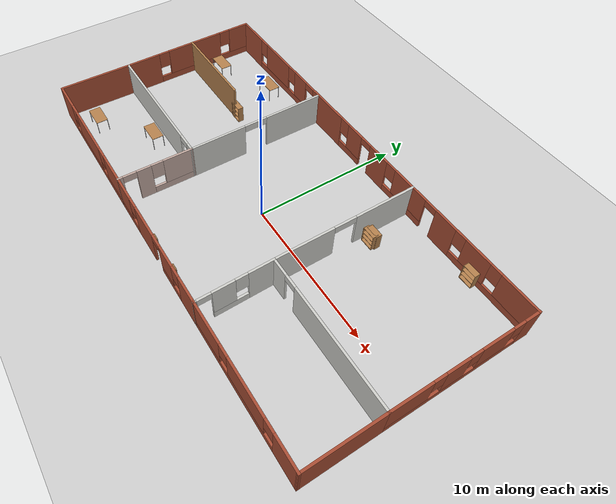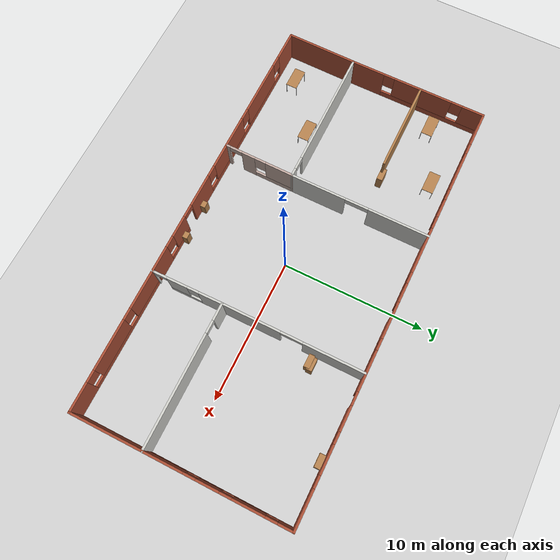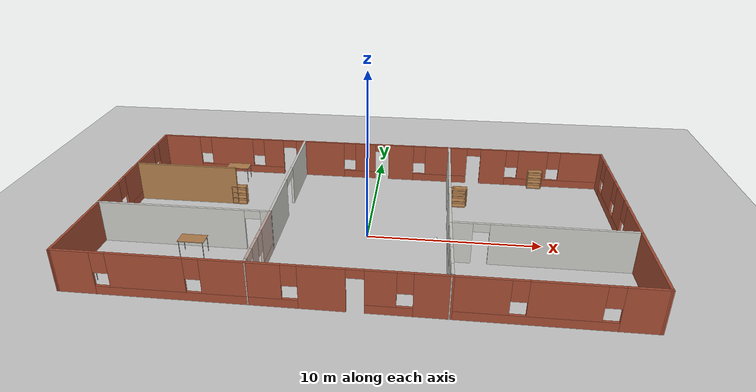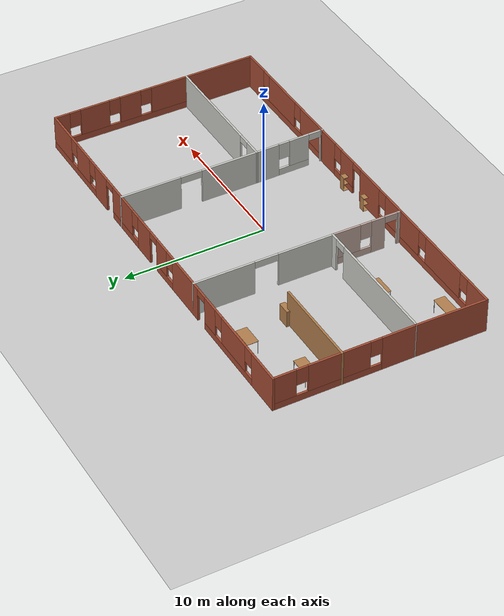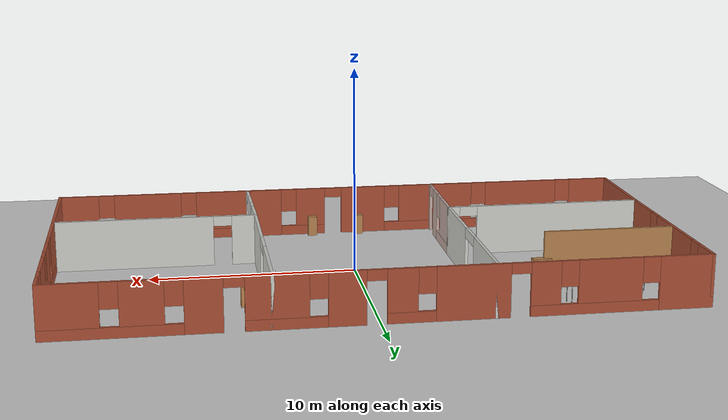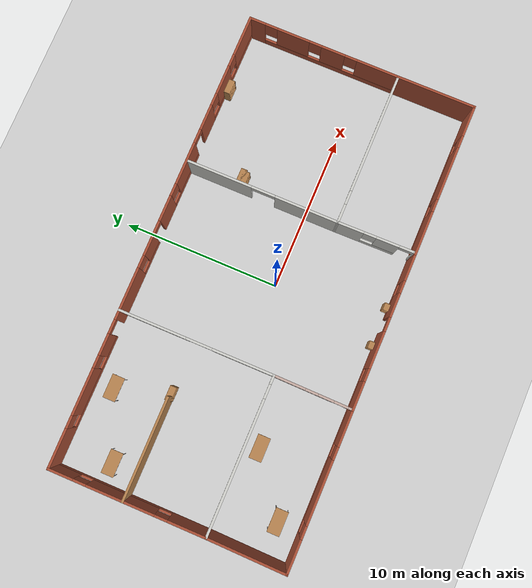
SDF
<sdf version="1.6">
 <world name="default">
  <light name="sun" type="directional">
   <pose>0 0 10 0 -0 0</pose>
   <diffuse>0.8 0.8 0.8 1</diffuse>
   <specular>0.2 0.2 0.2 1</specular>
   <attenuation>
    <range>1000</range>
    <constant>0.9</constant>
    <linear>0.01</linear>
    <quadratic>0.001</quadratic>
   </attenuation>
   <direction>-0.5 0.1 -0.9</direction>
  </light>
  <model name="ground_plane">
   <static>1</static>
   <link name="link">
    <collision name="collision">
     <geometry><plane><normal>0 0 1</normal><size>100 100</size></plane></geometry>
     <surface><friction><ode><mu>100</mu><mu2>50</mu2></ode></friction></surface>
    </collision>
    <visual name="visual">
     <cast_shadows>0</cast_shadows>
     <geometry><plane><normal>0 0 1</normal><size>100 100</size></plane></geometry>
     <material>
      <script><uri>file://media/materials/scripts/gazebo.material</uri><name>Gazebo/Grey</name></script>
     </material>
    </visual>
   </link>
  </model>
  <gravity>0 0 -9.8</gravity>
  <magnetic_field>6e-06 2.3e-05 -4.2e-05</magnetic_field>
  <atmosphere type="adiabatic"/>
  <physics name="default_physics" default="0" type="ode">
   <max_step_size>0.001</max_step_size>
   <real_time_factor>1</real_time_factor>
   <real_time_update_rate>1000</real_time_update_rate>
  </physics>
  <scene><ambient>0.4 0.4 0.4 1</ambient><background>0.7 0.7 0.7 1</background><shadows>1</shadows></scene>
  <spherical_coordinates>
   <surface_model>EARTH_WGS84</surface_model>
   <latitude_deg>0</latitude_deg>
   <longitude_deg>0</longitude_deg>
   <elevation>0</elevation>
   <heading_deg>0</heading_deg>
  </spherical_coordinates>
  <model name="model">
   <pose>-0.287073 0.38076 0 0 -0 0</pose>
   <link name="Wall_0">
    <pose>0.025373 7.41389 0 0 -0 0</pose>
    <visual name="Wall_0_Visual_0">
     <pose>-13.6006 0 1.25 0 -0 0</pose>
     <geometry><box><size>2.54886 0.15 2.5</size></box></geometry>
     <material>
      <script><uri>file://media/materials/scripts/gazebo.material</uri><name>Gazebo/Bricks</name></script>
      <ambient>1 1 1 1</ambient>
     </material>
     <meta><layer>0</layer></meta>
    </visual>
    <collision name="Wall_0_Collision_0">
     <geometry><box><size>2.54886 0.15 2.5</size></box></geometry>
     <pose>-13.6006 0 1.25 0 -0 0</pose>
    </collision>
    <visual name="Wall_0_Visual_1">
     <pose>-3.84098 0 1.25 0 -0 0</pose>
     <geometry><box><size>3.3339 0.15 2.5</size></box></geometry>
     <material>
      <script><uri>file://media/materials/scripts/gazebo.material</uri><name>Gazebo/Bricks</name></script>
      <ambient>1 1 1 1</ambient>
     </material>
     <meta><layer>0</layer></meta>
    </visual>
    <collision name="Wall_0_Collision_1">
     <geometry><box><size>3.3339 0.15 2.5</size></box></geometry>
     <pose>-3.84098 0 1.25 0 -0 0</pose>
    </collision>
    <visual name="Wall_0_Visual_2">
     <pose>1.72729 0 1.25 0 -0 0</pose>
     <geometry><box><size>1.67264 0.15 2.5</size></box></geometry>
     <material>
      <script><uri>file://media/materials/scripts/gazebo.material</uri><name>Gazebo/Bricks</name></script>
      <ambient>1 1 1 1</ambient>
     </material>
     <meta><layer>0</layer></meta>
    </visual>
    <collision name="Wall_0_Collision_2">
     <geometry><box><size>1.67264 0.15 2.5</size></box></geometry>
     <pose>1.72729 0 1.25 0 -0 0</pose>
    </collision>
    <visual name="Wall_0_Visual_3">
     <pose>7.88007 0 1.25 0 -0 0</pose>
     <geometry><box><size>1.67264 0.15 2.5</size></box></geometry>
     <material>
      <script><uri>file://media/materials/scripts/gazebo.material</uri><name>Gazebo/Bricks</name></script>
      <ambient>1 1 1 1</ambient>
     </material>
     <meta><layer>0</layer></meta>
    </visual>
    <collision name="Wall_0_Collision_3">
     <geometry><box><size>1.67264 0.15 2.5</size></box></geometry>
     <pose>7.88007 0 1.25 0 -0 0</pose>
    </collision>
    <visual name="Wall_0_Visual_4">
     <pose>-9.36703 0 0.25 0 -0 0</pose>
     <geometry><box><size>5.9182 0.15 0.5</size></box></geometry>
     <material>
      <script><uri>file://media/materials/scripts/gazebo.material</uri><name>Gazebo/Bricks</name></script>
      <ambient>1 1 1 1</ambient>
     </material>
     <meta><layer>0</layer></meta>
    </visual>
    <collision name="Wall_0_Collision_4">
     <geometry><box><size>5.9182 0.15 0.5</size></box></geometry>
     <pose>-9.36703 0 0.25 0 -0 0</pose>
    </collision>
    <visual name="Wall_0_Visual_5">
     <pose>-1.09154 0 0.25 0 -0 0</pose>
     <geometry><box><size>2.165 0.15 0.5</size></box></geometry>
     <material>
      <script><uri>file://media/materials/scripts/gazebo.material</uri><name>Gazebo/Bricks</name></script>
      <ambient>1 1 1 1</ambient>
     </material>
     <meta><layer>0</layer></meta>
    </visual>
    <collision name="Wall_0_Collision_5">
     <geometry><box><size>2.165 0.15 0.5</size></box></geometry>
     <pose>-1.09154 0 0.25 0 -0 0</pose>
    </collision>
    <visual name="Wall_0_Visual_6">
     <pose>4.35368 0 0.25 0 -0 0</pose>
     <geometry><box><size>3.58014 0.15 0.5</size></box></geometry>
     <material>
      <script><uri>file://media/materials/scripts/gazebo.material</uri><name>Gazebo/Bricks</name></script>
      <ambient>1 1 1 1</ambient>
     </material>
     <meta><layer>0</layer></meta>
    </visual>
    <collision name="Wall_0_Collision_6">
     <geometry><box><size>3.58014 0.15 0.5</size></box></geometry>
     <pose>4.35368 0 0.25 0 -0 0</pose>
    </collision>
    <visual name="Wall_0_Visual_7">
     <pose>11.7957 0 0.25 0 -0 0</pose>
     <geometry><box><size>6.1586 0.15 0.5</size></box></geometry>
     <material>
      <script><uri>file://media/materials/scripts/gazebo.material</uri><name>Gazebo/Bricks</name></script>
      <ambient>1 1 1 1</ambient>
     </material>
     <meta><layer>0</layer></meta>
    </visual>
    <collision name="Wall_0_Collision_7">
     <geometry><box><size>6.1586 0.15 0.5</size></box></geometry>
     <pose>11.7957 0 0.25 0 -0 0</pose>
    </collision>
    <visual name="Wall_0_Visual_8">
     <pose>-10.0495 0 1.5 0 -0 0</pose>
     <geometry><box><size>2.9532 0.15 2</size></box></geometry>
     <material>
      <script><uri>file://media/materials/scripts/gazebo.material</uri><name>Gazebo/Bricks</name></script>
      <ambient>1 1 1 1</ambient>
     </material>
     <meta><layer>0</layer></meta>
    </visual>
    <collision name="Wall_0_Collision_8">
     <geometry><box><size>2.9532 0.15 2</size></box></geometry>
     <pose>-10.0495 0 1.5 0 -0 0</pose>
    </collision>
    <visual name="Wall_0_Visual_9">
     <pose>-7.09043 0 1.5 0 -0 0</pose>
     <geometry><box><size>1.365 0.15 2</size></box></geometry>
     <material>
      <script><uri>file://media/materials/scripts/gazebo.material</uri><name>Gazebo/Bricks</name></script>
      <ambient>1 1 1 1</ambient>
     </material>
     <meta><layer>0</layer></meta>
    </visual>
    <collision name="Wall_0_Collision_9">
     <geometry><box><size>1.365 0.15 2</size></box></geometry>
     <pose>-7.09043 0 1.5 0 -0 0</pose>
    </collision>
    <visual name="Wall_0_Visual_10">
     <pose>-7.09043 0 1.5 0 -0 0</pose>
     <geometry><box><size>1.365 0.15 2</size></box></geometry>
     <material>
      <script><uri>file://media/materials/scripts/gazebo.material</uri><name>Gazebo/Bricks</name></script>
      <ambient>1 1 1 1</ambient>
     </material>
     <meta><layer>0</layer></meta>
    </visual>
    <collision name="Wall_0_Collision_10">
     <geometry><box><size>1.365 0.15 2</size></box></geometry>
     <pose>-7.09043 0 1.5 0 -0 0</pose>
    </collision>
    <visual name="Wall_0_Visual_11">
     <pose>-0.691536 0 1.5 0 -0 0</pose>
     <geometry><box><size>1.365 0.15 2</size></box></geometry>
     <material>
      <script><uri>file://media/materials/scripts/gazebo.material</uri><name>Gazebo/Bricks</name></script>
      <ambient>1 1 1 1</ambient>
     </material>
     <meta><layer>0</layer></meta>
    </visual>
    <collision name="Wall_0_Collision_11">
     <geometry><box><size>1.365 0.15 2</size></box></geometry>
     <pose>-0.691536 0 1.5 0 -0 0</pose>
    </collision>
    <visual name="Wall_0_Visual_12">
     <pose>-0.691536 0 1.5 0 -0 0</pose>
     <geometry><box><size>1.365 0.15 2</size></box></geometry>
     <material>
      <script><uri>file://media/materials/scripts/gazebo.material</uri><name>Gazebo/Bricks</name></script>
      <ambient>1 1 1 1</ambient>
     </material>
     <meta><layer>0</layer></meta>
    </visual>
    <collision name="Wall_0_Collision_12">
     <geometry><box><size>1.365 0.15 2</size></box></geometry>
     <pose>-0.691536 0 1.5 0 -0 0</pose>
    </collision>
    <visual name="Wall_0_Visual_13">
     <pose>4.75368 0 1.5 0 -0 0</pose>
     <geometry><box><size>2.78015 0.15 2</size></box></geometry>
     <material>
      <script><uri>file://media/materials/scripts/gazebo.material</uri><name>Gazebo/Bricks</name></script>
      <ambient>1 1 1 1</ambient>
     </material>
     <meta><layer>0</layer></meta>
    </visual>
    <collision name="Wall_0_Collision_13">
     <geometry><box><size>2.78015 0.15 2</size></box></geometry>
     <pose>4.75368 0 1.5 0 -0 0</pose>
    </collision>
    <visual name="Wall_0_Visual_14">
     <pose>4.75368 0 1.5 0 -0 0</pose>
     <geometry><box><size>2.78015 0.15 2</size></box></geometry>
     <material>
      <script><uri>file://media/materials/scripts/gazebo.material</uri><name>Gazebo/Bricks</name></script>
      <ambient>1 1 1 1</ambient>
     </material>
     <meta><layer>0</layer></meta>
    </visual>
    <collision name="Wall_0_Collision_14">
     <geometry><box><size>2.78015 0.15 2</size></box></geometry>
     <pose>4.75368 0 1.5 0 -0 0</pose>
    </collision>
    <visual name="Wall_0_Visual_15">
     <pose>10.47 0 1.5 0 -0 0</pose>
     <geometry><box><size>1.90723 0.15 2</size></box></geometry>
     <material>
      <script><uri>file://media/materials/scripts/gazebo.material</uri><name>Gazebo/Bricks</name></script>
      <ambient>1 1 1 1</ambient>
     </material>
     <meta><layer>0</layer></meta>
    </visual>
    <collision name="Wall_0_Collision_15">
     <geometry><box><size>1.90723 0.15 2</size></box></geometry>
     <pose>10.47 0 1.5 0 -0 0</pose>
    </collision>
    <visual name="Wall_0_Visual_16">
     <pose>13.5493 0 1.5 0 -0 0</pose>
     <geometry><box><size>2.65138 0.15 2</size></box></geometry>
     <material>
      <script><uri>file://media/materials/scripts/gazebo.material</uri><name>Gazebo/Bricks</name></script>
      <ambient>1 1 1 1</ambient>
     </material>
     <meta><layer>0</layer></meta>
    </visual>
    <collision name="Wall_0_Collision_16">
     <geometry><box><size>2.65138 0.15 2</size></box></geometry>
     <pose>13.5493 0 1.5 0 -0 0</pose>
    </collision>
    <visual name="Wall_0_Visual_17">
     <pose>-11.9261 0 1.9 0 -0 0</pose>
     <geometry><box><size>0.8 0.15 1.2</size></box></geometry>
     <material>
      <script><uri>file://media/materials/scripts/gazebo.material</uri><name>Gazebo/Bricks</name></script>
      <ambient>1 1 1 1</ambient>
     </material>
     <meta><layer>0</layer></meta>
    </visual>
    <collision name="Wall_0_Collision_17">
     <geometry><box><size>0.8 0.15 1.2</size></box></geometry>
     <pose>-11.9261 0 1.9 0 -0 0</pose>
    </collision>
    <visual name="Wall_0_Visual_18">
     <pose>-1.77404 0 1.9 0 -0 0</pose>
     <geometry><box><size>0.8 0.15 1.2</size></box></geometry>
     <material>
      <script><uri>file://media/materials/scripts/gazebo.material</uri><name>Gazebo/Bricks</name></script>
      <ambient>1 1 1 1</ambient>
     </material>
     <meta><layer>0</layer></meta>
    </visual>
    <collision name="Wall_0_Collision_18">
     <geometry><box><size>0.8 0.15 1.2</size></box></geometry>
     <pose>-1.77404 0 1.9 0 -0 0</pose>
    </collision>
    <visual name="Wall_0_Visual_19">
     <pose>2.96361 0 1.9 0 -0 0</pose>
     <geometry><box><size>0.8 0.15 1.2</size></box></geometry>
     <material>
      <script><uri>file://media/materials/scripts/gazebo.material</uri><name>Gazebo/Bricks</name></script>
      <ambient>1 1 1 1</ambient>
     </material>
     <meta><layer>0</layer></meta>
    </visual>
    <collision name="Wall_0_Collision_19">
     <geometry><box><size>0.8 0.15 1.2</size></box></geometry>
     <pose>2.96361 0 1.9 0 -0 0</pose>
    </collision>
    <visual name="Wall_0_Visual_20">
     <pose>9.1164 0 1.9 0 -0 0</pose>
     <geometry><box><size>0.8 0.15 1.2</size></box></geometry>
     <material>
      <script><uri>file://media/materials/scripts/gazebo.material</uri><name>Gazebo/Bricks</name></script>
      <ambient>1 1 1 1</ambient>
     </material>
     <meta><layer>0</layer></meta>
    </visual>
    <collision name="Wall_0_Collision_20">
     <geometry><box><size>0.8 0.15 1.2</size></box></geometry>
     <pose>9.1164 0 1.9 0 -0 0</pose>
    </collision>
    <visual name="Wall_0_Visual_21">
     <pose>-8.17294 0 1.9 0 -0 0</pose>
     <geometry><box><size>0.8 0.15 1.2</size></box></geometry>
     <material>
      <script><uri>file://media/materials/scripts/gazebo.material</uri><name>Gazebo/Bricks</name></script>
      <ambient>1 1 1 1</ambient>
     </material>
     <meta><layer>0</layer></meta>
    </visual>
    <collision name="Wall_0_Collision_21">
     <geometry><box><size>0.8 0.15 1.2</size></box></geometry>
     <pose>-8.17294 0 1.9 0 -0 0</pose>
    </collision>
    <visual name="Wall_0_Visual_22">
     <pose>11.8236 0 1.9 0 -0 0</pose>
     <geometry><box><size>0.8 0.15 1.2</size></box></geometry>
     <material>
      <script><uri>file://media/materials/scripts/gazebo.material</uri><name>Gazebo/Bricks</name></script>
      <ambient>1 1 1 1</ambient>
     </material>
     <meta><layer>0</layer></meta>
    </visual>
    <collision name="Wall_0_Collision_22">
     <geometry><box><size>0.8 0.15 1.2</size></box></geometry>
     <pose>11.8236 0 1.9 0 -0 0</pose>
    </collision>
    <visual name="Wall_0_Visual_23">
     <pose>-5.95793 0 2.25 0 -0 0</pose>
     <geometry><box><size>0.9 0.15 0.5</size></box></geometry>
     <material>
      <script><uri>file://media/materials/scripts/gazebo.material</uri><name>Gazebo/Bricks</name></script>
      <ambient>1 1 1 1</ambient>
     </material>
     <meta><layer>0</layer></meta>
    </visual>
    <collision name="Wall_0_Collision_23">
     <geometry><box><size>0.9 0.15 0.5</size></box></geometry>
     <pose>-5.95793 0 2.25 0 -0 0</pose>
    </collision>
    <visual name="Wall_0_Visual_24">
     <pose>-5.95793 0 2.25 0 -0 0</pose>
     <geometry><box><size>0.9 0.15 0.5</size></box></geometry>
     <material>
      <script><uri>file://media/materials/scripts/gazebo.material</uri><name>Gazebo/Bricks</name></script>
      <ambient>1 1 1 1</ambient>
     </material>
     <meta><layer>0</layer></meta>
    </visual>
    <collision name="Wall_0_Collision_24">
     <geometry><box><size>0.9 0.15 0.5</size></box></geometry>
     <pose>-5.95793 0 2.25 0 -0 0</pose>
    </collision>
    <visual name="Wall_0_Visual_25">
     <pose>0.440966 0 2.25 0 -0 0</pose>
     <geometry><box><size>0.9 0.15 0.5</size></box></geometry>
     <material>
      <script><uri>file://media/materials/scripts/gazebo.material</uri><name>Gazebo/Bricks</name></script>
      <ambient>1 1 1 1</ambient>
     </material>
     <meta><layer>0</layer></meta>
    </visual>
    <collision name="Wall_0_Collision_25">
     <geometry><box><size>0.9 0.15 0.5</size></box></geometry>
     <pose>0.440966 0 2.25 0 -0 0</pose>
    </collision>
    <visual name="Wall_0_Visual_26">
     <pose>0.440966 0 2.25 0 -0 0</pose>
     <geometry><box><size>0.9 0.15 0.5</size></box></geometry>
     <material>
      <script><uri>file://media/materials/scripts/gazebo.material</uri><name>Gazebo/Bricks</name></script>
      <ambient>1 1 1 1</ambient>
     </material>
     <meta><layer>0</layer></meta>
    </visual>
    <collision name="Wall_0_Collision_26">
     <geometry><box><size>0.9 0.15 0.5</size></box></geometry>
     <pose>0.440966 0 2.25 0 -0 0</pose>
    </collision>
    <visual name="Wall_0_Visual_27">
     <pose>6.59375 0 2.25 0 -0 0</pose>
     <geometry><box><size>0.9 0.15 0.5</size></box></geometry>
     <material>
      <script><uri>file://media/materials/scripts/gazebo.material</uri><name>Gazebo/Bricks</name></script>
      <ambient>1 1 1 1</ambient>
     </material>
     <meta><layer>0</layer></meta>
    </visual>
    <collision name="Wall_0_Collision_27">
     <geometry><box><size>0.9 0.15 0.5</size></box></geometry>
     <pose>6.59375 0 2.25 0 -0 0</pose>
    </collision>
    <visual name="Wall_0_Visual_28">
     <pose>6.59375 0 2.25 0 -0 0</pose>
     <geometry><box><size>0.9 0.15 0.5</size></box></geometry>
     <material>
      <script><uri>file://media/materials/scripts/gazebo.material</uri><name>Gazebo/Bricks</name></script>
      <ambient>1 1 1 1</ambient>
     </material>
     <meta><layer>0</layer></meta>
    </visual>
    <collision name="Wall_0_Collision_28">
     <geometry><box><size>0.9 0.15 0.5</size></box></geometry>
     <pose>6.59375 0 2.25 0 -0 0</pose>
    </collision>
   </link>
   <link name="Wall_1">
    <pose>14.8254 2.48889 0 0 0 -1.5708</pose>
    <visual name="Wall_1_Visual_0">
     <pose>-4.44963 0 1.25 0 -0 0</pose>
     <geometry><box><size>1.10073 0.15 2.5</size></box></geometry>
     <material>
      <script><uri>file://media/materials/scripts/gazebo.material</uri><name>Gazebo/Bricks</name></script>
      <ambient>1 1 1 1</ambient>
     </material>
     <meta><layer>0</layer></meta>
    </visual>
    <collision name="Wall_1_Collision_0">
     <geometry><box><size>1.10073 0.15 2.5</size></box></geometry>
     <pose>-4.44963 0 1.25 0 -0 0</pose>
    </collision>
    <visual name="Wall_1_Visual_1">
     <pose>0.550366 0 0.25 0 -0 0</pose>
     <geometry><box><size>8.89927 0.15 0.5</size></box></geometry>
     <material>
      <script><uri>file://media/materials/scripts/gazebo.material</uri><name>Gazebo/Bricks</name></script>
      <ambient>1 1 1 1</ambient>
     </material>
     <meta><layer>0</layer></meta>
    </visual>
    <collision name="Wall_1_Collision_1">
     <geometry><box><size>8.89927 0.15 0.5</size></box></geometry>
     <pose>0.550366 0 0.25 0 -0 0</pose>
    </collision>
    <visual name="Wall_1_Visual_2">
     <pose>-2.02795 0 1.5 0 -0 0</pose>
     <geometry><box><size>2.14264 0.15 2</size></box></geometry>
     <material>
      <script><uri>file://media/materials/scripts/gazebo.material</uri><name>Gazebo/Bricks</name></script>
      <ambient>1 1 1 1</ambient>
     </material>
     <meta><layer>0</layer></meta>
    </visual>
    <collision name="Wall_1_Collision_2">
     <geometry><box><size>2.14264 0.15 2</size></box></geometry>
     <pose>-2.02795 0 1.5 0 -0 0</pose>
    </collision>
    <visual name="Wall_1_Visual_3">
     <pose>0.620425 0 1.5 0 -0 0</pose>
     <geometry><box><size>1.55411 0.15 2</size></box></geometry>
     <material>
      <script><uri>file://media/materials/scripts/gazebo.material</uri><name>Gazebo/Bricks</name></script>
      <ambient>1 1 1 1</ambient>
     </material>
     <meta><layer>0</layer></meta>
    </visual>
    <collision name="Wall_1_Collision_3">
     <geometry><box><size>1.55411 0.15 2</size></box></geometry>
     <pose>0.620425 0 1.5 0 -0 0</pose>
    </collision>
    <visual name="Wall_1_Visual_4">
     <pose>3.59874 0 1.5 0 -0 0</pose>
     <geometry><box><size>2.80252 0.15 2</size></box></geometry>
     <material>
      <script><uri>file://media/materials/scripts/gazebo.material</uri><name>Gazebo/Bricks</name></script>
      <ambient>1 1 1 1</ambient>
     </material>
     <meta><layer>0</layer></meta>
    </visual>
    <collision name="Wall_1_Collision_4">
     <geometry><box><size>2.80252 0.15 2</size></box></geometry>
     <pose>3.59874 0 1.5 0 -0 0</pose>
    </collision>
    <visual name="Wall_1_Visual_5">
     <pose>-3.49927 0 1.9 0 -0 0</pose>
     <geometry><box><size>0.8 0.15 1.2</size></box></geometry>
     <material>
      <script><uri>file://media/materials/scripts/gazebo.material</uri><name>Gazebo/Bricks</name></script>
      <ambient>1 1 1 1</ambient>
     </material>
     <meta><layer>0</layer></meta>
    </visual>
    <collision name="Wall_1_Collision_5">
     <geometry><box><size>0.8 0.15 1.2</size></box></geometry>
     <pose>-3.49927 0 1.9 0 -0 0</pose>
    </collision>
    <visual name="Wall_1_Visual_6">
     <pose>-0.55663 0 1.9 0 -0 0</pose>
     <geometry><box><size>0.8 0.15 1.2</size></box></geometry>
     <material>
      <script><uri>file://media/materials/scripts/gazebo.material</uri><name>Gazebo/Bricks</name></script>
      <ambient>1 1 1 1</ambient>
     </material>
     <meta><layer>0</layer></meta>
    </visual>
    <collision name="Wall_1_Collision_6">
     <geometry><box><size>0.8 0.15 1.2</size></box></geometry>
     <pose>-0.55663 0 1.9 0 -0 0</pose>
    </collision>
    <visual name="Wall_1_Visual_7">
     <pose>1.79748 0 1.9 0 -0 0</pose>
     <geometry><box><size>0.8 0.15 1.2</size></box></geometry>
     <material>
      <script><uri>file://media/materials/scripts/gazebo.material</uri><name>Gazebo/Bricks</name></script>
      <ambient>1 1 1 1</ambient>
     </material>
     <meta><layer>0</layer></meta>
    </visual>
    <collision name="Wall_1_Collision_7">
     <geometry><box><size>0.8 0.15 1.2</size></box></geometry>
     <pose>1.79748 0 1.9 0 -0 0</pose>
    </collision>
   </link>
   <link name="Wall_11">
    <pose>4.97537 2.48889 0 0 -0 1.5708</pose>
    <visual name="Wall_11_Visual_0">
     <pose>-2.93024 0 1.25 0 -0 0</pose>
     <geometry><box><size>4.13951 0.15 2.5</size></box></geometry>
     <material>
      <script><uri>file://media/materials/scripts/gazebo.material</uri><name>Gazebo/CeilingTiled</name></script>
      <ambient>0.760784 0.662745 0.627451 1</ambient>
     </material>
     <meta><layer>0</layer></meta>
    </visual>
    <collision name="Wall_11_Collision_0">
     <geometry><box><size>4.13951 0.15 2.5</size></box></geometry>
     <pose>-2.93024 0 1.25 0 -0 0</pose>
    </collision>
    <visual name="Wall_11_Visual_1">
     <pose>2.83896 0 1.25 0 -0 0</pose>
     <geometry><box><size>4.32208 0.15 2.5</size></box></geometry>
     <material>
      <script><uri>file://media/materials/scripts/gazebo.material</uri><name>Gazebo/CeilingTiled</name></script>
      <ambient>0.760784 0.662745 0.627451 1</ambient>
     </material>
     <meta><layer>0</layer></meta>
    </visual>
    <collision name="Wall_11_Collision_1">
     <geometry><box><size>4.32208 0.15 2.5</size></box></geometry>
     <pose>2.83896 0 1.25 0 -0 0</pose>
    </collision>
    <visual name="Wall_11_Visual_2">
     <pose>-0.091286 0 2.25 0 -0 0</pose>
     <geometry><box><size>1.53841 0.15 0.5</size></box></geometry>
     <material>
      <script><uri>file://media/materials/scripts/gazebo.material</uri><name>Gazebo/CeilingTiled</name></script>
      <ambient>0.760784 0.662745 0.627451 1</ambient>
     </material>
     <meta><layer>0</layer></meta>
    </visual>
    <collision name="Wall_11_Collision_2">
     <geometry><box><size>1.53841 0.15 0.5</size></box></geometry>
     <pose>-0.091286 0 2.25 0 -0 0</pose>
    </collision>
   </link>
   <link name="Wall_13">
    <collision name="Wall_13_Collision">
     <geometry><box><size>6.5 0.15 2.5</size></box></geometry>
     <pose>0 0 1.25 0 -0 0</pose>
    </collision>
    <visual name="Wall_13_Visual">
     <pose>0 0 1.25 0 -0 0</pose>
     <geometry><box><size>6.5 0.15 2.5</size></box></geometry>
     <material>
      <script><uri>file://media/materials/scripts/gazebo.material</uri><name>Gazebo/Wood</name></script>
      <ambient>0.760784 0.662745 0.627451 1</ambient>
     </material>
     <meta><layer>0</layer></meta>
    </visual>
    <pose>-11.603 2.7386 0 0 -0 3.14159</pose>
   </link>
   <link name="Wall_15">
    <collision name="Wall_15_Collision">
     <geometry><box><size>5.12694 0.15 2.5</size></box></geometry>
     <pose>0 0 1.25 0 -0 0</pose>
    </collision>
    <visual name="Wall_15_Visual">
     <pose>0 0 1.25 0 -0 0</pose>
     <geometry><box><size>5.12694 0.15 2.5</size></box></geometry>
     <material>
      <script><uri>file://media/materials/scripts/gazebo.material</uri><name>Gazebo/Bricks</name></script>
      <ambient>1 1 1 1</ambient>
     </material>
     <meta><layer>0</layer></meta>
    </visual>
    <pose>-14.8054 -4.92459 0 0 0 -1.58316</pose>
   </link>
   <link name="Wall_16">
    <pose>-9.84963 -7.41306 0 0 -0 0</pose>
    <visual name="Wall_16_Visual_0">
     <pose>-3.95366 0 1.25 0 -0 0</pose>
     <geometry><box><size>2.09269 0.15 2.5</size></box></geometry>
     <material>
      <script><uri>file://media/materials/scripts/gazebo.material</uri><name>Gazebo/Bricks</name></script>
      <ambient>1 1 1 1</ambient>
     </material>
     <meta><layer>0</layer></meta>
    </visual>
    <collision name="Wall_16_Collision_0">
     <geometry><box><size>2.09269 0.15 2.5</size></box></geometry>
     <pose>-3.95366 0 1.25 0 -0 0</pose>
    </collision>
    <visual name="Wall_16_Visual_1">
     <pose>1.04634 0 0.25 0 -0 0</pose>
     <geometry><box><size>7.90731 0.15 0.5</size></box></geometry>
     <material>
      <script><uri>file://media/materials/scripts/gazebo.material</uri><name>Gazebo/Bricks</name></script>
      <ambient>1 1 1 1</ambient>
     </material>
     <meta><layer>0</layer></meta>
    </visual>
    <collision name="Wall_16_Collision_1">
     <geometry><box><size>7.90731 0.15 0.5</size></box></geometry>
     <pose>1.04634 0 0.25 0 -0 0</pose>
    </collision>
    <visual name="Wall_16_Visual_2">
     <pose>-0.126452 0 1.5 0 -0 0</pose>
     <geometry><box><size>3.96172 0.15 2</size></box></geometry>
     <material>
      <script><uri>file://media/materials/scripts/gazebo.material</uri><name>Gazebo/Bricks</name></script>
      <ambient>1 1 1 1</ambient>
     </material>
     <meta><layer>0</layer></meta>
    </visual>
    <collision name="Wall_16_Collision_2">
     <geometry><box><size>3.96172 0.15 2</size></box></geometry>
     <pose>-0.126452 0 1.5 0 -0 0</pose>
    </collision>
    <visual name="Wall_16_Visual_3">
     <pose>3.8272 0 1.5 0 -0 0</pose>
     <geometry><box><size>2.34559 0.15 2</size></box></geometry>
     <material>
      <script><uri>file://media/materials/scripts/gazebo.material</uri><name>Gazebo/Bricks</name></script>
      <ambient>1 1 1 1</ambient>
     </material>
     <meta><layer>0</layer></meta>
    </visual>
    <collision name="Wall_16_Collision_3">
     <geometry><box><size>2.34559 0.15 2</size></box></geometry>
     <pose>3.8272 0 1.5 0 -0 0</pose>
    </collision>
    <visual name="Wall_16_Visual_4">
     <pose>-2.50731 0 1.9 0 -0 0</pose>
     <geometry><box><size>0.8 0.15 1.2</size></box></geometry>
     <material>
      <script><uri>file://media/materials/scripts/gazebo.material</uri><name>Gazebo/Bricks</name></script>
      <ambient>1 1 1 1</ambient>
     </material>
     <meta><layer>0</layer></meta>
    </visual>
    <collision name="Wall_16_Collision_4">
     <geometry><box><size>0.8 0.15 1.2</size></box></geometry>
     <pose>-2.50731 0 1.9 0 -0 0</pose>
    </collision>
    <visual name="Wall_16_Visual_5">
     <pose>2.25441 0 1.9 0 -0 0</pose>
     <geometry><box><size>0.8 0.15 1.2</size></box></geometry>
     <material>
      <script><uri>file://media/materials/scripts/gazebo.material</uri><name>Gazebo/Bricks</name></script>
      <ambient>1 1 1 1</ambient>
     </material>
     <meta><layer>0</layer></meta>
    </visual>
    <collision name="Wall_16_Collision_5">
     <geometry><box><size>0.8 0.15 1.2</size></box></geometry>
     <pose>2.25441 0 1.9 0 -0 0</pose>
    </collision>
   </link>
   <link name="Wall_18">
    <collision name="Wall_18_Collision">
     <geometry><box><size>5.12696 0.15 2.5</size></box></geometry>
     <pose>0 0 1.25 0 -0 0</pose>
    </collision>
    <visual name="Wall_18_Visual">
     <pose>0 0 1.25 0 -0 0</pose>
     <geometry><box><size>5.12696 0.15 2.5</size></box></geometry>
     <material>
      <script><uri>file://media/materials/scripts/gazebo.material</uri><name>Gazebo/Bricks</name></script>
      <ambient>1 1 1 1</ambient>
     </material>
     <meta><layer>0</layer></meta>
    </visual>
    <pose>14.8311 -4.92459 0 0 0 -1.56848</pose>
   </link>
   <link name="Wall_19">
    <pose>9.9119 -7.41306 0 0 -0 3.14159</pose>
    <visual name="Wall_19_Visual_0">
     <pose>-3.97421 0 1.25 0 -0 0</pose>
     <geometry><box><size>2.05158 0.15 2.5</size></box></geometry>
     <material>
      <script><uri>file://media/materials/scripts/gazebo.material</uri><name>Gazebo/Bricks</name></script>
      <ambient>1 1 1 1</ambient>
     </material>
     <meta><layer>0</layer></meta>
    </visual>
    <collision name="Wall_19_Collision_0">
     <geometry><box><size>2.05158 0.15 2.5</size></box></geometry>
     <pose>-3.97421 0 1.25 0 -0 0</pose>
    </collision>
    <visual name="Wall_19_Visual_1">
     <pose>1.02579 0 0.25 0 -0 0</pose>
     <geometry><box><size>7.94842 0.15 0.5</size></box></geometry>
     <material>
      <script><uri>file://media/materials/scripts/gazebo.material</uri><name>Gazebo/Bricks</name></script>
      <ambient>1 1 1 1</ambient>
     </material>
     <meta><layer>0</layer></meta>
    </visual>
    <collision name="Wall_19_Collision_1">
     <geometry><box><size>7.94842 0.15 0.5</size></box></geometry>
     <pose>1.02579 0 0.25 0 -0 0</pose>
    </collision>
    <visual name="Wall_19_Visual_2">
     <pose>-0.4071 0 1.5 0 -0 0</pose>
     <geometry><box><size>3.48263 0.15 2</size></box></geometry>
     <material>
      <script><uri>file://media/materials/scripts/gazebo.material</uri><name>Gazebo/Bricks</name></script>
      <ambient>1 1 1 1</ambient>
     </material>
     <meta><layer>0</layer></meta>
    </visual>
    <collision name="Wall_19_Collision_2">
     <geometry><box><size>3.48263 0.15 2</size></box></geometry>
     <pose>-0.4071 0 1.5 0 -0 0</pose>
    </collision>
    <visual name="Wall_19_Visual_3">
     <pose>3.56711 0 1.5 0 -0 0</pose>
     <geometry><box><size>2.86578 0.15 2</size></box></geometry>
     <material>
      <script><uri>file://media/materials/scripts/gazebo.material</uri><name>Gazebo/Bricks</name></script>
      <ambient>1 1 1 1</ambient>
     </material>
     <meta><layer>0</layer></meta>
    </visual>
    <collision name="Wall_19_Collision_3">
     <geometry><box><size>2.86578 0.15 2</size></box></geometry>
     <pose>3.56711 0 1.5 0 -0 0</pose>
    </collision>
    <visual name="Wall_19_Visual_4">
     <pose>-2.54842 0 1.9 0 -0 0</pose>
     <geometry><box><size>0.8 0.15 1.2</size></box></geometry>
     <material>
      <script><uri>file://media/materials/scripts/gazebo.material</uri><name>Gazebo/Bricks</name></script>
      <ambient>1 1 1 1</ambient>
     </material>
     <meta><layer>0</layer></meta>
    </visual>
    <collision name="Wall_19_Collision_4">
     <geometry><box><size>0.8 0.15 1.2</size></box></geometry>
     <pose>-2.54842 0 1.9 0 -0 0</pose>
    </collision>
    <visual name="Wall_19_Visual_5">
     <pose>1.73422 0 1.9 0 -0 0</pose>
     <geometry><box><size>0.8 0.15 1.2</size></box></geometry>
     <material>
      <script><uri>file://media/materials/scripts/gazebo.material</uri><name>Gazebo/Bricks</name></script>
      <ambient>1 1 1 1</ambient>
     </material>
     <meta><layer>0</layer></meta>
    </visual>
    <collision name="Wall_19_Collision_5">
     <geometry><box><size>0.8 0.15 1.2</size></box></geometry>
     <pose>1.73422 0 1.9 0 -0 0</pose>
    </collision>
   </link>
   <link name="Wall_2">
    <pose>9.90037 -2.43611 0 0 -0 3.14159</pose>
    <visual name="Wall_2_Visual_0">
     <pose>-1.08438 0 1.25 0 -0 0</pose>
     <geometry><box><size>7.83125 0.15 2.5</size></box></geometry>
     <material>
      <script><uri>file://media/materials/scripts/gazebo.material</uri><name>Gazebo/CeilingTiled</name></script>
      <ambient>0.921569 0.807843 0.615686 1</ambient>
     </material>
     <meta><layer>0</layer></meta>
    </visual>
    <collision name="Wall_2_Collision_0">
     <geometry><box><size>7.83125 0.15 2.5</size></box></geometry>
     <pose>-1.08438 0 1.25 0 -0 0</pose>
    </collision>
    <visual name="Wall_2_Visual_1">
     <pose>4.36562 0 1.25 0 -0 0</pose>
     <geometry><box><size>1.26875 0.15 2.5</size></box></geometry>
     <material>
      <script><uri>file://media/materials/scripts/gazebo.material</uri><name>Gazebo/CeilingTiled</name></script>
      <ambient>0.921569 0.807843 0.615686 1</ambient>
     </material>
     <meta><layer>0</layer></meta>
    </visual>
    <collision name="Wall_2_Collision_1">
     <geometry><box><size>1.26875 0.15 2.5</size></box></geometry>
     <pose>4.36562 0 1.25 0 -0 0</pose>
    </collision>
    <visual name="Wall_2_Visual_2">
     <pose>3.28125 0 2.25 0 -0 0</pose>
     <geometry><box><size>0.9 0.15 0.5</size></box></geometry>
     <material>
      <script><uri>file://media/materials/scripts/gazebo.material</uri><name>Gazebo/CeilingTiled</name></script>
      <ambient>0.921569 0.807843 0.615686 1</ambient>
     </material>
     <meta><layer>0</layer></meta>
    </visual>
    <collision name="Wall_2_Collision_2">
     <geometry><box><size>0.9 0.15 0.5</size></box></geometry>
     <pose>3.28125 0 2.25 0 -0 0</pose>
    </collision>
   </link>
   <link name="Wall_3">
    <pose>5.0119 -4.92459 0 0 0 -1.55612</pose>
    <visual name="Wall_3_Visual_0">
     <pose>-1.68748 0 1.25 0 -0 0</pose>
     <geometry><box><size>1.75199 0.15 2.5</size></box></geometry>
     <material>
      <script><uri>file://media/materials/scripts/gazebo.material</uri><name>Gazebo/CeilingTiled</name></script>
      <ambient>0.760784 0.662745 0.627451 1</ambient>
     </material>
     <meta><layer>0</layer></meta>
    </visual>
    <collision name="Wall_3_Collision_0">
     <geometry><box><size>1.75199 0.15 2.5</size></box></geometry>
     <pose>-1.68748 0 1.25 0 -0 0</pose>
    </collision>
    <visual name="Wall_3_Visual_1">
     <pose>2.45614 0 1.25 0 -0 0</pose>
     <geometry><box><size>0.214679 0.15 2.5</size></box></geometry>
     <material>
      <script><uri>file://media/materials/scripts/gazebo.material</uri><name>Gazebo/CeilingTiled</name></script>
      <ambient>0.760784 0.662745 0.627451 1</ambient>
     </material>
     <meta><layer>0</layer></meta>
    </visual>
    <collision name="Wall_3_Collision_1">
     <geometry><box><size>0.214679 0.15 2.5</size></box></geometry>
     <pose>2.45614 0 1.25 0 -0 0</pose>
    </collision>
    <visual name="Wall_3_Visual_2">
     <pose>0.318654 0 0.25 0 -0 0</pose>
     <geometry><box><size>2.26029 0.15 0.5</size></box></geometry>
     <material>
      <script><uri>file://media/materials/scripts/gazebo.material</uri><name>Gazebo/CeilingTiled</name></script>
      <ambient>0.760784 0.662745 0.627451 1</ambient>
     </material>
     <meta><layer>0</layer></meta>
    </visual>
    <collision name="Wall_3_Collision_2">
     <geometry><box><size>2.26029 0.15 0.5</size></box></geometry>
     <pose>0.318654 0 0.25 0 -0 0</pose>
    </collision>
    <visual name="Wall_3_Visual_3">
     <pose>0.718654 0 1.5 0 -0 0</pose>
     <geometry><box><size>1.46029 0.15 2</size></box></geometry>
     <material>
      <script><uri>file://media/materials/scripts/gazebo.material</uri><name>Gazebo/CeilingTiled</name></script>
      <ambient>0.760784 0.662745 0.627451 1</ambient>
     </material>
     <meta><layer>0</layer></meta>
    </visual>
    <collision name="Wall_3_Collision_3">
     <geometry><box><size>1.46029 0.15 2</size></box></geometry>
     <pose>0.718654 0 1.5 0 -0 0</pose>
    </collision>
    <visual name="Wall_3_Visual_4">
     <pose>-0.411491 0 1.9 0 -0 0</pose>
     <geometry><box><size>0.8 0.15 1.2</size></box></geometry>
     <material>
      <script><uri>file://media/materials/scripts/gazebo.material</uri><name>Gazebo/CeilingTiled</name></script>
      <ambient>0.760784 0.662745 0.627451 1</ambient>
     </material>
     <meta><layer>0</layer></meta>
    </visual>
    <collision name="Wall_3_Collision_4">
     <geometry><box><size>0.8 0.15 1.2</size></box></geometry>
     <pose>-0.411491 0 1.9 0 -0 0</pose>
    </collision>
    <visual name="Wall_3_Visual_5">
     <pose>1.8988 0 2.25 0 -0 0</pose>
     <geometry><box><size>0.9 0.15 0.5</size></box></geometry>
     <material>
      <script><uri>file://media/materials/scripts/gazebo.material</uri><name>Gazebo/CeilingTiled</name></script>
      <ambient>0.760784 0.662745 0.627451 1</ambient>
     </material>
     <meta><layer>0</layer></meta>
    </visual>
    <collision name="Wall_3_Collision_5">
     <geometry><box><size>0.9 0.15 0.5</size></box></geometry>
     <pose>1.8988 0 2.25 0 -0 0</pose>
    </collision>
   </link>
   <link name="Wall_4">
    <pose>0.061901 -7.41306 0 0 -0 3.14159</pose>
    <visual name="Wall_4_Visual_0">
     <pose>-4.12498 0 1.25 0 -0 0</pose>
     <geometry><box><size>1.8731 0.15 2.5</size></box></geometry>
     <material>
      <script><uri>file://media/materials/scripts/gazebo.material</uri><name>Gazebo/Bricks</name></script>
      <ambient>1 1 1 1</ambient>
     </material>
     <meta><layer>0</layer></meta>
    </visual>
    <collision name="Wall_4_Collision_0">
     <geometry><box><size>1.8731 0.15 2.5</size></box></geometry>
     <pose>-4.12498 0 1.25 0 -0 0</pose>
    </collision>
    <visual name="Wall_4_Visual_1">
     <pose>1.23719 0 1.25 0 -0 0</pose>
     <geometry><box><size>2.36213 0.15 2.5</size></box></geometry>
     <material>
      <script><uri>file://media/materials/scripts/gazebo.material</uri><name>Gazebo/Bricks</name></script>
      <ambient>1 1 1 1</ambient>
     </material>
     <meta><layer>0</layer></meta>
    </visual>
    <collision name="Wall_4_Collision_1">
     <geometry><box><size>2.36213 0.15 2.5</size></box></geometry>
     <pose>1.23719 0 1.25 0 -0 0</pose>
    </collision>
    <visual name="Wall_4_Visual_2">
     <pose>-2.01615 0 0.25 0 -0 0</pose>
     <geometry><box><size>2.34456 0.15 0.5</size></box></geometry>
     <material>
      <script><uri>file://media/materials/scripts/gazebo.material</uri><name>Gazebo/Bricks</name></script>
      <ambient>1 1 1 1</ambient>
     </material>
     <meta><layer>0</layer></meta>
    </visual>
    <collision name="Wall_4_Collision_2">
     <geometry><box><size>2.34456 0.15 0.5</size></box></geometry>
     <pose>-2.01615 0 0.25 0 -0 0</pose>
    </collision>
    <visual name="Wall_4_Visual_3">
     <pose>3.73989 0 0.25 0 -0 0</pose>
     <geometry><box><size>2.64327 0.15 0.5</size></box></geometry>
     <material>
      <script><uri>file://media/materials/scripts/gazebo.material</uri><name>Gazebo/Bricks</name></script>
      <ambient>1 1 1 1</ambient>
     </material>
     <meta><layer>0</layer></meta>
    </visual>
    <collision name="Wall_4_Collision_3">
     <geometry><box><size>2.64327 0.15 0.5</size></box></geometry>
     <pose>3.73989 0 0.25 0 -0 0</pose>
    </collision>
    <visual name="Wall_4_Visual_4">
     <pose>-1.61615 0 1.5 0 -0 0</pose>
     <geometry><box><size>1.54456 0.15 2</size></box></geometry>
     <material>
      <script><uri>file://media/materials/scripts/gazebo.material</uri><name>Gazebo/Bricks</name></script>
      <ambient>1 1 1 1</ambient>
     </material>
     <meta><layer>0</layer></meta>
    </visual>
    <collision name="Wall_4_Collision_4">
     <geometry><box><size>1.54456 0.15 2</size></box></geometry>
     <pose>-1.61615 0 1.5 0 -0 0</pose>
    </collision>
    <visual name="Wall_4_Visual_5">
     <pose>-1.61615 0 1.5 0 -0 0</pose>
     <geometry><box><size>1.54456 0.15 2</size></box></geometry>
     <material>
      <script><uri>file://media/materials/scripts/gazebo.material</uri><name>Gazebo/Bricks</name></script>
      <ambient>1 1 1 1</ambient>
     </material>
     <meta><layer>0</layer></meta>
    </visual>
    <collision name="Wall_4_Collision_5">
     <geometry><box><size>1.54456 0.15 2</size></box></geometry>
     <pose>-1.61615 0 1.5 0 -0 0</pose>
    </collision>
    <visual name="Wall_4_Visual_6">
     <pose>4.13989 0 1.5 0 -0 0</pose>
     <geometry><box><size>1.84327 0.15 2</size></box></geometry>
     <material>
      <script><uri>file://media/materials/scripts/gazebo.material</uri><name>Gazebo/Bricks</name></script>
      <ambient>1 1 1 1</ambient>
     </material>
     <meta><layer>0</layer></meta>
    </visual>
    <collision name="Wall_4_Collision_6">
     <geometry><box><size>1.84327 0.15 2</size></box></geometry>
     <pose>4.13989 0 1.5 0 -0 0</pose>
    </collision>
    <visual name="Wall_4_Visual_7">
     <pose>-2.78843 0 1.9 0 -0 0</pose>
     <geometry><box><size>0.8 0.15 1.2</size></box></geometry>
     <material>
      <script><uri>file://media/materials/scripts/gazebo.material</uri><name>Gazebo/Bricks</name></script>
      <ambient>1 1 1 1</ambient>
     </material>
     <meta><layer>0</layer></meta>
    </visual>
    <collision name="Wall_4_Collision_7">
     <geometry><box><size>0.8 0.15 1.2</size></box></geometry>
     <pose>-2.78843 0 1.9 0 -0 0</pose>
    </collision>
    <visual name="Wall_4_Visual_8">
     <pose>2.81826 0 1.9 0 -0 0</pose>
     <geometry><box><size>0.8 0.15 1.2</size></box></geometry>
     <material>
      <script><uri>file://media/materials/scripts/gazebo.material</uri><name>Gazebo/Bricks</name></script>
      <ambient>1 1 1 1</ambient>
     </material>
     <meta><layer>0</layer></meta>
    </visual>
    <collision name="Wall_4_Collision_8">
     <geometry><box><size>0.8 0.15 1.2</size></box></geometry>
     <pose>2.81826 0 1.9 0 -0 0</pose>
    </collision>
    <visual name="Wall_4_Visual_9">
     <pose>-0.393873 0 2.25 0 -0 0</pose>
     <geometry><box><size>0.9 0.15 0.5</size></box></geometry>
     <material>
      <script><uri>file://media/materials/scripts/gazebo.material</uri><name>Gazebo/Bricks</name></script>
      <ambient>1 1 1 1</ambient>
     </material>
     <meta><layer>0</layer></meta>
    </visual>
    <collision name="Wall_4_Collision_9">
     <geometry><box><size>0.9 0.15 0.5</size></box></geometry>
     <pose>-0.393873 0 2.25 0 -0 0</pose>
    </collision>
    <visual name="Wall_4_Visual_10">
     <pose>-0.393873 0 2.25 0 -0 0</pose>
     <geometry><box><size>0.9 0.15 0.5</size></box></geometry>
     <material>
      <script><uri>file://media/materials/scripts/gazebo.material</uri><name>Gazebo/Bricks</name></script>
      <ambient>1 1 1 1</ambient>
     </material>
     <meta><layer>0</layer></meta>
    </visual>
    <collision name="Wall_4_Collision_10">
     <geometry><box><size>0.9 0.15 0.5</size></box></geometry>
     <pose>-0.393873 0 2.25 0 -0 0</pose>
    </collision>
   </link>
   <link name="Wall_5">
    <pose>-4.89963 -4.92459 0 0 -0 1.56075</pose>
    <visual name="Wall_5_Visual_0">
     <pose>-2.37557 0 1.25 0 -0 0</pose>
     <geometry><box><size>0.376054 0.15 2.5</size></box></geometry>
     <material>
      <script><uri>file://media/materials/scripts/gazebo.material</uri><name>Gazebo/Grey</name></script>
      <ambient>0.760784 0.662745 0.627451 1</ambient>
     </material>
     <meta><layer>0</layer></meta>
    </visual>
    <collision name="Wall_5_Collision_0">
     <geometry><box><size>0.376054 0.15 2.5</size></box></geometry>
     <pose>-2.37557 0 1.25 0 -0 0</pose>
    </collision>
    <visual name="Wall_5_Visual_1">
     <pose>-0.795891 0 1.25 0 -0 0</pose>
     <geometry><box><size>0.983304 0.15 2.5</size></box></geometry>
     <material>
      <script><uri>file://media/materials/scripts/gazebo.material</uri><name>Gazebo/Grey</name></script>
      <ambient>0.760784 0.662745 0.627451 1</ambient>
     </material>
     <meta><layer>0</layer></meta>
    </visual>
    <collision name="Wall_5_Collision_1">
     <geometry><box><size>0.983304 0.15 2.5</size></box></geometry>
     <pose>-0.795891 0 1.25 0 -0 0</pose>
    </collision>
    <visual name="Wall_5_Visual_2">
     <pose>1.12968 0 0.25 0 -0 0</pose>
     <geometry><box><size>2.86784 0.15 0.5</size></box></geometry>
     <material>
      <script><uri>file://media/materials/scripts/gazebo.material</uri><name>Gazebo/Grey</name></script>
      <ambient>0.760784 0.662745 0.627451 1</ambient>
     </material>
     <meta><layer>0</layer></meta>
    </visual>
    <collision name="Wall_5_Collision_2">
     <geometry><box><size>2.86784 0.15 0.5</size></box></geometry>
     <pose>1.12968 0 0.25 0 -0 0</pose>
    </collision>
    <visual name="Wall_5_Visual_3">
     <pose>1.52968 0 1.5 0 -0 0</pose>
     <geometry><box><size>2.06784 0.15 2</size></box></geometry>
     <material>
      <script><uri>file://media/materials/scripts/gazebo.material</uri><name>Gazebo/Grey</name></script>
      <ambient>0.760784 0.662745 0.627451 1</ambient>
     </material>
     <meta><layer>0</layer></meta>
    </visual>
    <collision name="Wall_5_Collision_3">
     <geometry><box><size>2.06784 0.15 2</size></box></geometry>
     <pose>1.52968 0 1.5 0 -0 0</pose>
    </collision>
    <visual name="Wall_5_Visual_4">
     <pose>0.09576 0 1.9 0 -0 0</pose>
     <geometry><box><size>0.8 0.15 1.2</size></box></geometry>
     <material>
      <script><uri>file://media/materials/scripts/gazebo.material</uri><name>Gazebo/Grey</name></script>
      <ambient>0.760784 0.662745 0.627451 1</ambient>
     </material>
     <meta><layer>0</layer></meta>
    </visual>
    <collision name="Wall_5_Collision_4">
     <geometry><box><size>0.8 0.15 1.2</size></box></geometry>
     <pose>0.09576 0 1.9 0 -0 0</pose>
    </collision>
    <visual name="Wall_5_Visual_5">
     <pose>-1.73754 0 2.25 0 -0 0</pose>
     <geometry><box><size>0.9 0.15 0.5</size></box></geometry>
     <material>
      <script><uri>file://media/materials/scripts/gazebo.material</uri><name>Gazebo/Grey</name></script>
      <ambient>0.760784 0.662745 0.627451 1</ambient>
     </material>
     <meta><layer>0</layer></meta>
    </visual>
    <collision name="Wall_5_Collision_5">
     <geometry><box><size>0.9 0.15 0.5</size></box></geometry>
     <pose>-1.73754 0 2.25 0 -0 0</pose>
    </collision>
   </link>
   <link name="Wall_6">
    <pose>-9.82463 -2.43611 0 0 -0 3.14159</pose>
    <visual name="Wall_6_Visual_0">
     <pose>-4.7143 0 1.25 0 -0 0</pose>
     <geometry><box><size>0.621405 0.15 2.5</size></box></geometry>
     <material>
      <script><uri>file://media/materials/scripts/gazebo.material</uri><name>Gazebo/CeilingTiled</name></script>
      <ambient>0.996078 0.47451 0.0196078 1</ambient>
     </material>
     <meta><layer>0</layer></meta>
    </visual>
    <collision name="Wall_6_Collision_0">
     <geometry><box><size>0.621405 0.15 2.5</size></box></geometry>
     <pose>-4.7143 0 1.25 0 -0 0</pose>
    </collision>
    <visual name="Wall_6_Visual_1">
     <pose>0.760702 0 1.25 0 -0 0</pose>
     <geometry><box><size>8.52859 0.15 2.5</size></box></geometry>
     <material>
      <script><uri>file://media/materials/scripts/gazebo.material</uri><name>Gazebo/CeilingTiled</name></script>
      <ambient>0.996078 0.47451 0.0196078 1</ambient>
     </material>
     <meta><layer>0</layer></meta>
    </visual>
    <collision name="Wall_6_Collision_1">
     <geometry><box><size>8.52859 0.15 2.5</size></box></geometry>
     <pose>0.760702 0 1.25 0 -0 0</pose>
    </collision>
    <visual name="Wall_6_Visual_2">
     <pose>-3.95359 0 2.25 0 -0 0</pose>
     <geometry><box><size>0.9 0.15 0.5</size></box></geometry>
     <material>
      <script><uri>file://media/materials/scripts/gazebo.material</uri><name>Gazebo/CeilingTiled</name></script>
      <ambient>0.996078 0.47451 0.0196078 1</ambient>
     </material>
     <meta><layer>0</layer></meta>
    </visual>
    <collision name="Wall_6_Collision_2">
     <geometry><box><size>0.9 0.15 0.5</size></box></geometry>
     <pose>-3.95359 0 2.25 0 -0 0</pose>
    </collision>
   </link>
   <link name="Wall_7">
    <pose>-14.7746 2.48889 0 0 -0 1.5708</pose>
    <visual name="Wall_7_Visual_0">
     <pose>-3.75925 0 1.25 0 -0 0</pose>
     <geometry><box><size>2.4815 0.15 2.5</size></box></geometry>
     <material>
      <script><uri>file://media/materials/scripts/gazebo.material</uri><name>Gazebo/Bricks</name></script>
      <ambient>1 1 1 1</ambient>
     </material>
     <meta><layer>0</layer></meta>
    </visual>
    <collision name="Wall_7_Collision_0">
     <geometry><box><size>2.4815 0.15 2.5</size></box></geometry>
     <pose>-3.75925 0 1.25 0 -0 0</pose>
    </collision>
    <visual name="Wall_7_Visual_1">
     <pose>1.24075 0 0.25 0 -0 0</pose>
     <geometry><box><size>7.51849 0.15 0.5</size></box></geometry>
     <material>
      <script><uri>file://media/materials/scripts/gazebo.material</uri><name>Gazebo/Bricks</name></script>
      <ambient>1 1 1 1</ambient>
     </material>
     <meta><layer>0</layer></meta>
    </visual>
    <collision name="Wall_7_Collision_1">
     <geometry><box><size>7.51849 0.15 0.5</size></box></geometry>
     <pose>1.24075 0 0.25 0 -0 0</pose>
    </collision>
    <visual name="Wall_7_Visual_2">
     <pose>0.422874 0 1.5 0 -0 0</pose>
     <geometry><box><size>4.28274 0.15 2</size></box></geometry>
     <material>
      <script><uri>file://media/materials/scripts/gazebo.material</uri><name>Gazebo/Bricks</name></script>
      <ambient>1 1 1 1</ambient>
     </material>
     <meta><layer>0</layer></meta>
    </visual>
    <collision name="Wall_7_Collision_2">
     <geometry><box><size>4.28274 0.15 2</size></box></geometry>
     <pose>0.422874 0 1.5 0 -0 0</pose>
    </collision>
    <visual name="Wall_7_Visual_3">
     <pose>4.18212 0 1.5 0 -0 0</pose>
     <geometry><box><size>1.63576 0.15 2</size></box></geometry>
     <material>
      <script><uri>file://media/materials/scripts/gazebo.material</uri><name>Gazebo/Bricks</name></script>
      <ambient>1 1 1 1</ambient>
     </material>
     <meta><layer>0</layer></meta>
    </visual>
    <collision name="Wall_7_Collision_3">
     <geometry><box><size>1.63576 0.15 2</size></box></geometry>
     <pose>4.18212 0 1.5 0 -0 0</pose>
    </collision>
    <visual name="Wall_7_Visual_4">
     <pose>-2.11849 0 1.9 0 -0 0</pose>
     <geometry><box><size>0.8 0.15 1.2</size></box></geometry>
     <material>
      <script><uri>file://media/materials/scripts/gazebo.material</uri><name>Gazebo/Bricks</name></script>
      <ambient>1 1 1 1</ambient>
     </material>
     <meta><layer>0</layer></meta>
    </visual>
    <collision name="Wall_7_Collision_4">
     <geometry><box><size>0.8 0.15 1.2</size></box></geometry>
     <pose>-2.11849 0 1.9 0 -0 0</pose>
    </collision>
    <visual name="Wall_7_Visual_5">
     <pose>2.96424 0 1.9 0 -0 0</pose>
     <geometry><box><size>0.8 0.15 1.2</size></box></geometry>
     <material>
      <script><uri>file://media/materials/scripts/gazebo.material</uri><name>Gazebo/Bricks</name></script>
      <ambient>1 1 1 1</ambient>
     </material>
     <meta><layer>0</layer></meta>
    </visual>
    <collision name="Wall_7_Collision_5">
     <geometry><box><size>0.8 0.15 1.2</size></box></geometry>
     <pose>2.96424 0 1.9 0 -0 0</pose>
    </collision>
   </link>
   <link name="Wall_9">
    <pose>-4.87463 2.48889 0 0 -0 1.5708</pose>
    <visual name="Wall_9_Visual_0">
     <pose>-2.99773 0 1.25 0 -0 0</pose>
     <geometry><box><size>4.00453 0.15 2.5</size></box></geometry>
     <material>
      <script><uri>file://media/materials/scripts/gazebo.material</uri><name>Gazebo/CeilingTiled</name></script>
      <ambient>1 1 1 1</ambient>
     </material>
     <meta><layer>0</layer></meta>
    </visual>
    <collision name="Wall_9_Collision_0">
     <geometry><box><size>4.00453 0.15 2.5</size></box></geometry>
     <pose>-2.99773 0 1.25 0 -0 0</pose>
    </collision>
    <visual name="Wall_9_Visual_1">
     <pose>2.83208 0 1.25 0 -0 0</pose>
     <geometry><box><size>4.33584 0.15 2.5</size></box></geometry>
     <material>
      <script><uri>file://media/materials/scripts/gazebo.material</uri><name>Gazebo/CeilingTiled</name></script>
      <ambient>1 1 1 1</ambient>
     </material>
     <meta><layer>0</layer></meta>
    </visual>
    <collision name="Wall_9_Collision_1">
     <geometry><box><size>4.33584 0.15 2.5</size></box></geometry>
     <pose>2.83208 0 1.25 0 -0 0</pose>
    </collision>
    <visual name="Wall_9_Visual_2">
     <pose>-0.165653 0 2.25 0 -0 0</pose>
     <geometry><box><size>1.65963 0.15 0.5</size></box></geometry>
     <material>
      <script><uri>file://media/materials/scripts/gazebo.material</uri><name>Gazebo/CeilingTiled</name></script>
      <ambient>1 1 1 1</ambient>
     </material>
     <meta><layer>0</layer></meta>
    </visual>
    <collision name="Wall_9_Collision_2">
     <geometry><box><size>1.65963 0.15 0.5</size></box></geometry>
     <pose>-0.165653 0 2.25 0 -0 0</pose>
    </collision>
   </link>
   <static>1</static>
  </model>
  <model name="bookshelf">
   <static>1</static>
   <link name="link">
    <inertial><mass>1</mass></inertial>
    <collision name="back">
     <pose>0 0.005 0.6 0 -0 0</pose>
     <geometry><box><size>0.9 0.01 1.2</size></box></geometry>
    </collision>
    <visual name="visual1">
     <pose>0 0.005 0.6 0 -0 0</pose>
     <geometry><box><size>0.9 0.01 1.2</size></box></geometry>
     <material>
      <script><uri>file://media/materials/scripts/gazebo.material</uri><name>Gazebo/Wood</name></script>
     </material>
    </visual>
    <collision name="left_side">
     <pose>0.45 -0.195 0.6 0 -0 0</pose>
     <geometry><box><size>0.02 0.4 1.2</size></box></geometry>
    </collision>
    <visual name="visual2">
     <pose>0.45 -0.195 0.6 0 -0 0</pose>
     <geometry><box><size>0.02 0.4 1.2</size></box></geometry>
     <material>
      <script><uri>file://media/materials/scripts/gazebo.material</uri><name>Gazebo/Wood</name></script>
     </material>
    </visual>
    <collision name="right_side">
     <pose>-0.45 -0.195 0.6 0 -0 0</pose>
     <geometry><box><size>0.02 0.4 1.2</size></box></geometry>
    </collision>
    <visual name="visual3">
     <pose>-0.45 -0.195 0.6 0 -0 0</pose>
     <geometry><box><size>0.02 0.4 1.2</size></box></geometry>
     <material>
      <script><uri>file://media/materials/scripts/gazebo.material</uri><name>Gazebo/Wood</name></script>
     </material>
    </visual>
    <collision name="bottom">
     <pose>0 -0.195 0.03 0 -0 0</pose>
     <geometry><box><size>0.88 0.4 0.06</size></box></geometry>
    </collision>
    <visual name="visual4">
     <pose>0 -0.195 0.03 0 -0 0</pose>
     <geometry><box><size>0.88 0.4 0.06</size></box></geometry>
     <material>
      <script><uri>file://media/materials/scripts/gazebo.material</uri><name>Gazebo/Wood</name></script>
     </material>
    </visual>
    <collision name="top">
     <pose>0 -0.195 1.19 0 -0 0</pose>
     <geometry><box><size>0.88 0.4 0.02</size></box></geometry>
    </collision>
    <visual name="visual5">
     <pose>0 -0.195 1.19 0 -0 0</pose>
     <geometry><box><size>0.88 0.4 0.02</size></box></geometry>
     <material>
      <script><uri>file://media/materials/scripts/gazebo.material</uri><name>Gazebo/Wood</name></script>
     </material>
    </visual>
    <collision name="low_shelf">
     <pose>0 -0.195 0.43 0 -0 0</pose>
     <geometry><box><size>0.88 0.4 0.02</size></box></geometry>
    </collision>
    <visual name="visual6">
     <pose>0 -0.195 0.43 0 -0 0</pose>
     <geometry><box><size>0.88 0.4 0.02</size></box></geometry>
     <material>
      <script><uri>file://media/materials/scripts/gazebo.material</uri><name>Gazebo/Wood</name></script>
     </material>
    </visual>
    <collision name="high_shelf">
     <pose>0 -0.195 0.8 0 -0 0</pose>
     <geometry><box><size>0.88 0.4 0.02</size></box></geometry>
    </collision>
    <visual name="visual7">
     <pose>0 -0.195 0.8 0 -0 0</pose>
     <geometry><box><size>0.88 0.4 0.02</size></box></geometry>
     <material>
      <script><uri>file://media/materials/scripts/gazebo.material</uri><name>Gazebo/Wood</name></script>
     </material>
    </visual>
   </link>
   <pose>-8.52294 3.40116 0 0 -0 0</pose>
  </model>
  <model name="table_0">
   <static>1</static>
   <link name="link">
    <collision name="surface">
     <pose>0 0 1 0 -0 0</pose>
     <geometry><box><size>1.5 0.8 0.03</size></box></geometry>
     <surface><friction><ode><mu>0.6</mu><mu2>0.6</mu2></ode></friction></surface>
    </collision>
    <visual name="visual1">
     <pose>0 0 1 0 -0 0</pose>
     <geometry><box><size>1.5 0.8 0.03</size></box></geometry>
     <material>
      <script><uri>file://media/materials/scripts/gazebo.material</uri><name>Gazebo/Wood</name></script>
     </material>
    </visual>
    <collision name="front_left_leg">
     <pose>0.68 0.38 0.5 0 -0 0</pose>
     <geometry><cylinder><radius>0.02</radius><length>1</length></cylinder></geometry>
    </collision>
    <visual name="front_left_leg">
     <pose>0.68 0.38 0.5 0 -0 0</pose>
     <geometry><cylinder><radius>0.02</radius><length>1</length></cylinder></geometry>
     <material>
      <script><uri>file://media/materials/scripts/gazebo.material</uri><name>Gazebo/Grey</name></script>
     </material>
    </visual>
    <collision name="front_right_leg">
     <pose>0.68 -0.38 0.5 0 -0 0</pose>
     <geometry><cylinder><radius>0.02</radius><length>1</length></cylinder></geometry>
    </collision>
    <visual name="front_right_leg">
     <pose>0.68 -0.38 0.5 0 -0 0</pose>
     <geometry><cylinder><radius>0.02</radius><length>1</length></cylinder></geometry>
     <material>
      <script><uri>file://media/materials/scripts/gazebo.material</uri><name>Gazebo/Grey</name></script>
     </material>
    </visual>
    <collision name="back_right_leg">
     <pose>-0.68 -0.38 0.5 0 -0 0</pose>
     <geometry><cylinder><radius>0.02</radius><length>1</length></cylinder></geometry>
    </collision>
    <visual name="back_right_leg">
     <pose>-0.68 -0.38 0.5 0 -0 0</pose>
     <geometry><cylinder><radius>0.02</radius><length>1</length></cylinder></geometry>
     <material>
      <script><uri>file://media/materials/scripts/gazebo.material</uri><name>Gazebo/Grey</name></script>
     </material>
    </visual>
    <collision name="back_left_leg">
     <pose>-0.68 0.38 0.5 0 -0 0</pose>
     <geometry><cylinder><radius>0.02</radius><length>1</length></cylinder></geometry>
    </collision>
    <visual name="back_left_leg">
     <pose>-0.68 0.38 0.5 0 -0 0</pose>
     <geometry><cylinder><radius>0.02</radius><length>1</length></cylinder></geometry>
     <material>
      <script><uri>file://media/materials/scripts/gazebo.material</uri><name>Gazebo/Grey</name></script>
     </material>
    </visual>
   </link>
   <pose>-13.6033 4.76301 0 0 -0 0</pose>
  </model>
  <model name="table_1">
   <static>1</static>
   <link name="link">
    <collision name="surface">
     <pose>0 0 1 0 -0 0</pose>
     <geometry><box><size>1.5 0.8 0.03</size></box></geometry>
     <surface><friction><ode><mu>0.6</mu><mu2>0.6</mu2></ode></friction></surface>
    </collision>
    <visual name="visual1">
     <pose>0 0 1 0 -0 0</pose>
     <geometry><box><size>1.5 0.8 0.03</size></box></geometry>
     <material>
      <script><uri>file://media/materials/scripts/gazebo.material</uri><name>Gazebo/Wood</name></script>
     </material>
    </visual>
    <collision name="front_left_leg">
     <pose>0.68 0.38 0.5 0 -0 0</pose>
     <geometry><cylinder><radius>0.02</radius><length>1</length></cylinder></geometry>
    </collision>
    <visual name="front_left_leg">
     <pose>0.68 0.38 0.5 0 -0 0</pose>
     <geometry><cylinder><radius>0.02</radius><length>1</length></cylinder></geometry>
     <material>
      <script><uri>file://media/materials/scripts/gazebo.material</uri><name>Gazebo/Grey</name></script>
     </material>
    </visual>
    <collision name="front_right_leg">
     <pose>0.68 -0.38 0.5 0 -0 0</pose>
     <geometry><cylinder><radius>0.02</radius><length>1</length></cylinder></geometry>
    </collision>
    <visual name="front_right_leg">
     <pose>0.68 -0.38 0.5 0 -0 0</pose>
     <geometry><cylinder><radius>0.02</radius><length>1</length></cylinder></geometry>
     <material>
      <script><uri>file://media/materials/scripts/gazebo.material</uri><name>Gazebo/Grey</name></script>
     </material>
    </visual>
    <collision name="back_right_leg">
     <pose>-0.68 -0.38 0.5 0 -0 0</pose>
     <geometry><cylinder><radius>0.02</radius><length>1</length></cylinder></geometry>
    </collision>
    <visual name="back_right_leg">
     <pose>-0.68 -0.38 0.5 0 -0 0</pose>
     <geometry><cylinder><radius>0.02</radius><length>1</length></cylinder></geometry>
     <material>
      <script><uri>file://media/materials/scripts/gazebo.material</uri><name>Gazebo/Grey</name></script>
     </material>
    </visual>
    <collision name="back_left_leg">
     <pose>-0.68 0.38 0.5 0 -0 0</pose>
     <geometry><cylinder><radius>0.02</radius><length>1</length></cylinder></geometry>
    </collision>
    <visual name="back_left_leg">
     <pose>-0.68 0.38 0.5 0 -0 0</pose>
     <geometry><cylinder><radius>0.02</radius><length>1</length></cylinder></geometry>
     <material>
      <script><uri>file://media/materials/scripts/gazebo.material</uri><name>Gazebo/Grey</name></script>
     </material>
    </visual>
   </link>
   <pose>-9.54652 6.49752 0 0 -0 0</pose>
  </model>
  <model name="table_3">
   <static>1</static>
   <link name="link">
    <collision name="surface">
     <pose>0 0 1 0 -0 0</pose>
     <geometry><box><size>1.5 0.8 0.03</size></box></geometry>
     <surface><friction><ode><mu>0.6</mu><mu2>0.6</mu2></ode></friction></surface>
    </collision>
    <visual name="visual1">
     <pose>0 0 1 0 -0 0</pose>
     <geometry><box><size>1.5 0.8 0.03</size></box></geometry>
     <material>
      <script><uri>file://media/materials/scripts/gazebo.material</uri><name>Gazebo/Wood</name></script>
     </material>
    </visual>
    <collision name="front_left_leg">
     <pose>0.68 0.38 0.5 0 -0 0</pose>
     <geometry><cylinder><radius>0.02</radius><length>1</length></cylinder></geometry>
    </collision>
    <visual name="front_left_leg">
     <pose>0.68 0.38 0.5 0 -0 0</pose>
     <geometry><cylinder><radius>0.02</radius><length>1</length></cylinder></geometry>
     <material>
      <script><uri>file://media/materials/scripts/gazebo.material</uri><name>Gazebo/Grey</name></script>
     </material>
    </visual>
    <collision name="front_right_leg">
     <pose>0.68 -0.38 0.5 0 -0 0</pose>
     <geometry><cylinder><radius>0.02</radius><length>1</length></cylinder></geometry>
    </collision>
    <visual name="front_right_leg">
     <pose>0.68 -0.38 0.5 0 -0 0</pose>
     <geometry><cylinder><radius>0.02</radius><length>1</length></cylinder></geometry>
     <material>
      <script><uri>file://media/materials/scripts/gazebo.material</uri><name>Gazebo/Grey</name></script>
     </material>
    </visual>
    <collision name="back_right_leg">
     <pose>-0.68 -0.38 0.5 0 -0 0</pose>
     <geometry><cylinder><radius>0.02</radius><length>1</length></cylinder></geometry>
    </collision>
    <visual name="back_right_leg">
     <pose>-0.68 -0.38 0.5 0 -0 0</pose>
     <geometry><cylinder><radius>0.02</radius><length>1</length></cylinder></geometry>
     <material>
      <script><uri>file://media/materials/scripts/gazebo.material</uri><name>Gazebo/Grey</name></script>
     </material>
    </visual>
    <collision name="back_left_leg">
     <pose>-0.68 0.38 0.5 0 -0 0</pose>
     <geometry><cylinder><radius>0.02</radius><length>1</length></cylinder></geometry>
    </collision>
    <visual name="back_left_leg">
     <pose>-0.68 0.38 0.5 0 -0 0</pose>
     <geometry><cylinder><radius>0.02</radius><length>1</length></cylinder></geometry>
     <material>
      <script><uri>file://media/materials/scripts/gazebo.material</uri><name>Gazebo/Grey</name></script>
     </material>
    </visual>
   </link>
   <pose>-9.41374 -2.94265 0 0 -0 0</pose>
  </model>
  <model name="table_6">
   <static>1</static>
   <link name="link">
    <collision name="surface">
     <pose>0 0 1 0 -0 0</pose>
     <geometry><box><size>1.5 0.8 0.03</size></box></geometry>
     <surface><friction><ode><mu>0.6</mu><mu2>0.6</mu2></ode></friction></surface>
    </collision>
    <visual name="visual1">
     <pose>0 0 1 0 -0 0</pose>
     <geometry><box><size>1.5 0.8 0.03</size></box></geometry>
     <material>
      <script><uri>file://media/materials/scripts/gazebo.material</uri><name>Gazebo/Wood</name></script>
     </material>
    </visual>
    <collision name="front_left_leg">
     <pose>0.68 0.38 0.5 0 -0 0</pose>
     <geometry><cylinder><radius>0.02</radius><length>1</length></cylinder></geometry>
    </collision>
    <visual name="front_left_leg">
     <pose>0.68 0.38 0.5 0 -0 0</pose>
     <geometry><cylinder><radius>0.02</radius><length>1</length></cylinder></geometry>
     <material>
      <script><uri>file://media/materials/scripts/gazebo.material</uri><name>Gazebo/Grey</name></script>
     </material>
    </visual>
    <collision name="front_right_leg">
     <pose>0.68 -0.38 0.5 0 -0 0</pose>
     <geometry><cylinder><radius>0.02</radius><length>1</length></cylinder></geometry>
    </collision>
    <visual name="front_right_leg">
     <pose>0.68 -0.38 0.5 0 -0 0</pose>
     <geometry><cylinder><radius>0.02</radius><length>1</length></cylinder></geometry>
     <material>
      <script><uri>file://media/materials/scripts/gazebo.material</uri><name>Gazebo/Grey</name></script>
     </material>
    </visual>
    <collision name="back_right_leg">
     <pose>-0.68 -0.38 0.5 0 -0 0</pose>
     <geometry><cylinder><radius>0.02</radius><length>1</length></cylinder></geometry>
    </collision>
    <visual name="back_right_leg">
     <pose>-0.68 -0.38 0.5 0 -0 0</pose>
     <geometry><cylinder><radius>0.02</radius><length>1</length></cylinder></geometry>
     <material>
      <script><uri>file://media/materials/scripts/gazebo.material</uri><name>Gazebo/Grey</name></script>
     </material>
    </visual>
    <collision name="back_left_leg">
     <pose>-0.68 0.38 0.5 0 -0 0</pose>
     <geometry><cylinder><radius>0.02</radius><length>1</length></cylinder></geometry>
    </collision>
    <visual name="back_left_leg">
     <pose>-0.68 0.38 0.5 0 -0 0</pose>
     <geometry><cylinder><radius>0.02</radius><length>1</length></cylinder></geometry>
     <material>
      <script><uri>file://media/materials/scripts/gazebo.material</uri><name>Gazebo/Grey</name></script>
     </material>
    </visual>
   </link>
   <pose>-12.9112 -5.56317 0 0 -0 0</pose>
  </model>
  <model name="cabinet">
   <static>1</static>
   <link name="cabinet_bottom_plate">
    <inertial>
     <pose>0 0 -1 0 -0 0</pose>
     <inertia><ixx>2.05</ixx><ixy>0</ixy><ixz>0</ixz><iyy>2.05</iyy><iyz>0</iyz><izz>2.05</izz></inertia>
     <mass>25</mass>
    </inertial>
    <collision name="cabinet_bottom_plate_geom">
     <pose>0 0 0.01 0 -0 0</pose>
     <geometry><box><size>0.45 0.45 0.02</size></box></geometry>
    </collision>
    <visual name="cabinet_bottom_plate_geom_visual">
     <pose>0 0 0.01 0 -0 0</pose>
     <geometry><box><size>0.45 0.45 0.02</size></box></geometry>
     <material>
      <script><uri>file://media/materials/scripts/gazebo.material</uri><name>Gazebo/Wood</name></script>
     </material>
    </visual>
    <collision name="cabinet_bottom_plate_geom_cabinet_back_plate">
     <pose>0.235 0 0.51 0 -0 0</pose>
     <geometry><box><size>0.02 0.45 1.02</size></box></geometry>
    </collision>
    <visual name="cabinet_bottom_plate_geom_cabinet_back_plate_visual">
     <pose>0.235 0 0.51 0 -0 0</pose>
     <geometry><box><size>0.02 0.45 1.02</size></box></geometry>
     <material>
      <script><uri>file://media/materials/scripts/gazebo.material</uri><name>Gazebo/Wood</name></script>
     </material>
    </visual>
    <collision name="cabinet_bottom_plate_geom_cabinet_left_plate">
     <pose>0 0.235 0.51 0 -0 0</pose>
     <geometry><box><size>0.45 0.02 1.02</size></box></geometry>
    </collision>
    <visual name="cabinet_bottom_plate_geom_cabinet_left_plate_visual">
     <pose>0 0.235 0.51 0 -0 0</pose>
     <geometry><box><size>0.45 0.02 1.02</size></box></geometry>
     <material>
      <script><uri>file://media/materials/scripts/gazebo.material</uri><name>Gazebo/Wood</name></script>
     </material>
    </visual>
    <collision name="cabinet_bottom_plate_geom_cabinet_middle_plate">
     <pose>0 0 0.51 0 -0 0</pose>
     <geometry><box><size>0.45 0.45 0.02</size></box></geometry>
    </collision>
    <visual name="cabinet_bottom_plate_geom_cabinet_middle_plate_visual">
     <pose>0 0 0.51 0 -0 0</pose>
     <geometry><box><size>0.45 0.45 0.02</size></box></geometry>
     <material>
      <script><uri>file://media/materials/scripts/gazebo.material</uri><name>Gazebo/Wood</name></script>
     </material>
    </visual>
    <collision name="cabinet_bottom_plate_geom_cabinet_right_plate">
     <pose>0 -0.235 0.51 0 -0 0</pose>
     <geometry><box><size>0.45 0.02 1.02</size></box></geometry>
    </collision>
    <visual name="cabinet_bottom_plate_geom_cabinet_right_plate_visual">
     <pose>0 -0.235 0.51 0 -0 0</pose>
     <geometry><box><size>0.45 0.02 1.02</size></box></geometry>
     <material>
      <script><uri>file://media/materials/scripts/gazebo.material</uri><name>Gazebo/Wood</name></script>
     </material>
    </visual>
    <collision name="cabinet_bottom_plate_geom_cabinet_top_plate">
     <pose>0 0 1.01 0 -0 0</pose>
     <geometry><box><size>0.45 0.45 0.02</size></box></geometry>
    </collision>
    <visual name="cabinet_bottom_plate_geom_cabinet_top_plate_visual">
     <pose>0 0 1.01 0 -0 0</pose>
     <geometry><box><size>0.45 0.45 0.02</size></box></geometry>
     <material>
      <script><uri>file://media/materials/scripts/gazebo.material</uri><name>Gazebo/Wood</name></script>
     </material>
    </visual>
   </link>
   <pose>1.31083 -6.83157 0 0 -0 0</pose>
  </model>
  <model name="cabinet_0">
   <static>1</static>
   <link name="cabinet_bottom_plate">
    <inertial>
     <pose>0 0 -1 0 -0 0</pose>
     <inertia><ixx>2.05</ixx><ixy>0</ixy><ixz>0</ixz><iyy>2.05</iyy><iyz>0</iyz><izz>2.05</izz></inertia>
     <mass>25</mass>
    </inertial>
    <collision name="cabinet_bottom_plate_geom">
     <pose>0 0 0.01 0 -0 0</pose>
     <geometry><box><size>0.45 0.45 0.02</size></box></geometry>
    </collision>
    <visual name="cabinet_bottom_plate_geom_visual">
     <pose>0 0 0.01 0 -0 0</pose>
     <geometry><box><size>0.45 0.45 0.02</size></box></geometry>
     <material>
      <script><uri>file://media/materials/scripts/gazebo.material</uri><name>Gazebo/Wood</name></script>
     </material>
    </visual>
    <collision name="cabinet_bottom_plate_geom_cabinet_back_plate">
     <pose>0.235 0 0.51 0 -0 0</pose>
     <geometry><box><size>0.02 0.45 1.02</size></box></geometry>
    </collision>
    <visual name="cabinet_bottom_plate_geom_cabinet_back_plate_visual">
     <pose>0.235 0 0.51 0 -0 0</pose>
     <geometry><box><size>0.02 0.45 1.02</size></box></geometry>
     <material>
      <script><uri>file://media/materials/scripts/gazebo.material</uri><name>Gazebo/Wood</name></script>
     </material>
    </visual>
    <collision name="cabinet_bottom_plate_geom_cabinet_left_plate">
     <pose>0 0.235 0.51 0 -0 0</pose>
     <geometry><box><size>0.45 0.02 1.02</size></box></geometry>
    </collision>
    <visual name="cabinet_bottom_plate_geom_cabinet_left_plate_visual">
     <pose>0 0.235 0.51 0 -0 0</pose>
     <geometry><box><size>0.45 0.02 1.02</size></box></geometry>
     <material>
      <script><uri>file://media/materials/scripts/gazebo.material</uri><name>Gazebo/Wood</name></script>
     </material>
    </visual>
    <collision name="cabinet_bottom_plate_geom_cabinet_middle_plate">
     <pose>0 0 0.51 0 -0 0</pose>
     <geometry><box><size>0.45 0.45 0.02</size></box></geometry>
    </collision>
    <visual name="cabinet_bottom_plate_geom_cabinet_middle_plate_visual">
     <pose>0 0 0.51 0 -0 0</pose>
     <geometry><box><size>0.45 0.45 0.02</size></box></geometry>
     <material>
      <script><uri>file://media/materials/scripts/gazebo.material</uri><name>Gazebo/Wood</name></script>
     </material>
    </visual>
    <collision name="cabinet_bottom_plate_geom_cabinet_right_plate">
     <pose>0 -0.235 0.51 0 -0 0</pose>
     <geometry><box><size>0.45 0.02 1.02</size></box></geometry>
    </collision>
    <visual name="cabinet_bottom_plate_geom_cabinet_right_plate_visual">
     <pose>0 -0.235 0.51 0 -0 0</pose>
     <geometry><box><size>0.45 0.02 1.02</size></box></geometry>
     <material>
      <script><uri>file://media/materials/scripts/gazebo.material</uri><name>Gazebo/Wood</name></script>
     </material>
    </visual>
    <collision name="cabinet_bottom_plate_geom_cabinet_top_plate">
     <pose>0 0 1.01 0 -0 0</pose>
     <geometry><box><size>0.45 0.45 0.02</size></box></geometry>
    </collision>
    <visual name="cabinet_bottom_plate_geom_cabinet_top_plate_visual">
     <pose>0 0 1.01 0 -0 0</pose>
     <geometry><box><size>0.45 0.45 0.02</size></box></geometry>
     <material>
      <script><uri>file://media/materials/scripts/gazebo.material</uri><name>Gazebo/Wood</name></script>
     </material>
    </visual>
   </link>
   <pose>-1.19186 -6.83845 0 0 -0 0</pose>
  </model>
  <model name="bookshelf_0">
   <static>1</static>
   <link name="link">
    <inertial><mass>1</mass></inertial>
    <collision name="back">
     <pose>0 0.005 0.6 0 -0 0</pose>
     <geometry><box><size>0.9 0.01 1.2</size></box></geometry>
    </collision>
    <visual name="visual1">
     <pose>0 0.005 0.6 0 -0 0</pose>
     <geometry><box><size>0.9 0.01 1.2</size></box></geometry>
     <material>
      <script><uri>file://media/materials/scripts/gazebo.material</uri><name>Gazebo/Wood</name></script>
     </material>
    </visual>
    <collision name="left_side">
     <pose>0.45 -0.195 0.6 0 -0 0</pose>
     <geometry><box><size>0.02 0.4 1.2</size></box></geometry>
    </collision>
    <visual name="visual2">
     <pose>0.45 -0.195 0.6 0 -0 0</pose>
     <geometry><box><size>0.02 0.4 1.2</size></box></geometry>
     <material>
      <script><uri>file://media/materials/scripts/gazebo.material</uri><name>Gazebo/Wood</name></script>
     </material>
    </visual>
    <collision name="right_side">
     <pose>-0.45 -0.195 0.6 0 -0 0</pose>
     <geometry><box><size>0.02 0.4 1.2</size></box></geometry>
    </collision>
    <visual name="visual3">
     <pose>-0.45 -0.195 0.6 0 -0 0</pose>
     <geometry><box><size>0.02 0.4 1.2</size></box></geometry>
     <material>
      <script><uri>file://media/materials/scripts/gazebo.material</uri><name>Gazebo/Wood</name></script>
     </material>
    </visual>
    <collision name="bottom">
     <pose>0 -0.195 0.03 0 -0 0</pose>
     <geometry><box><size>0.88 0.4 0.06</size></box></geometry>
    </collision>
    <visual name="visual4">
     <pose>0 -0.195 0.03 0 -0 0</pose>
     <geometry><box><size>0.88 0.4 0.06</size></box></geometry>
     <material>
      <script><uri>file://media/materials/scripts/gazebo.material</uri><name>Gazebo/Wood</name></script>
     </material>
    </visual>
    <collision name="top">
     <pose>0 -0.195 1.19 0 -0 0</pose>
     <geometry><box><size>0.88 0.4 0.02</size></box></geometry>
    </collision>
    <visual name="visual5">
     <pose>0 -0.195 1.19 0 -0 0</pose>
     <geometry><box><size>0.88 0.4 0.02</size></box></geometry>
     <material>
      <script><uri>file://media/materials/scripts/gazebo.material</uri><name>Gazebo/Wood</name></script>
     </material>
    </visual>
    <collision name="low_shelf">
     <pose>0 -0.195 0.43 0 -0 0</pose>
     <geometry><box><size>0.88 0.4 0.02</size></box></geometry>
    </collision>
    <visual name="visual6">
     <pose>0 -0.195 0.43 0 -0 0</pose>
     <geometry><box><size>0.88 0.4 0.02</size></box></geometry>
     <material>
      <script><uri>file://media/materials/scripts/gazebo.material</uri><name>Gazebo/Wood</name></script>
     </material>
    </visual>
    <collision name="high_shelf">
     <pose>0 -0.195 0.8 0 -0 0</pose>
     <geometry><box><size>0.88 0.4 0.02</size></box></geometry>
    </collision>
    <visual name="visual7">
     <pose>0 -0.195 0.8 0 -0 0</pose>
     <geometry><box><size>0.88 0.4 0.02</size></box></geometry>
     <material>
      <script><uri>file://media/materials/scripts/gazebo.material</uri><name>Gazebo/Wood</name></script>
     </material>
    </visual>
   </link>
   <pose>10.4249 7.70807 0 0 -0 0</pose>
  </model>
  <model name="bookshelf_1">
   <static>1</static>
   <link name="link">
    <inertial><mass>1</mass></inertial>
    <collision name="back">
     <pose>0 0.005 0.6 0 -0 0</pose>
     <geometry><box><size>0.9 0.01 1.2</size></box></geometry>
    </collision>
    <visual name="visual1">
     <pose>0 0.005 0.6 0 -0 0</pose>
     <geometry><box><size>0.9 0.01 1.2</size></box></geometry>
     <material>
      <script><uri>file://media/materials/scripts/gazebo.material</uri><name>Gazebo/Wood</name></script>
     </material>
    </visual>
    <collision name="left_side">
     <pose>0.45 -0.195 0.6 0 -0 0</pose>
     <geometry><box><size>0.02 0.4 1.2</size></box></geometry>
    </collision>
    <visual name="visual2">
     <pose>0.45 -0.195 0.6 0 -0 0</pose>
     <geometry><box><size>0.02 0.4 1.2</size></box></geometry>
     <material>
      <script><uri>file://media/materials/scripts/gazebo.material</uri><name>Gazebo/Wood</name></script>
     </material>
    </visual>
    <collision name="right_side">
     <pose>-0.45 -0.195 0.6 0 -0 0</pose>
     <geometry><box><size>0.02 0.4 1.2</size></box></geometry>
    </collision>
    <visual name="visual3">
     <pose>-0.45 -0.195 0.6 0 -0 0</pose>
     <geometry><box><size>0.02 0.4 1.2</size></box></geometry>
     <material>
      <script><uri>file://media/materials/scripts/gazebo.material</uri><name>Gazebo/Wood</name></script>
     </material>
    </visual>
    <collision name="bottom">
     <pose>0 -0.195 0.03 0 -0 0</pose>
     <geometry><box><size>0.88 0.4 0.06</size></box></geometry>
    </collision>
    <visual name="visual4">
     <pose>0 -0.195 0.03 0 -0 0</pose>
     <geometry><box><size>0.88 0.4 0.06</size></box></geometry>
     <material>
      <script><uri>file://media/materials/scripts/gazebo.material</uri><name>Gazebo/Wood</name></script>
     </material>
    </visual>
    <collision name="top">
     <pose>0 -0.195 1.19 0 -0 0</pose>
     <geometry><box><size>0.88 0.4 0.02</size></box></geometry>
    </collision>
    <visual name="visual5">
     <pose>0 -0.195 1.19 0 -0 0</pose>
     <geometry><box><size>0.88 0.4 0.02</size></box></geometry>
     <material>
      <script><uri>file://media/materials/scripts/gazebo.material</uri><name>Gazebo/Wood</name></script>
     </material>
    </visual>
    <collision name="low_shelf">
     <pose>0 -0.195 0.43 0 -0 0</pose>
     <geometry><box><size>0.88 0.4 0.02</size></box></geometry>
    </collision>
    <visual name="visual6">
     <pose>0 -0.195 0.43 0 -0 0</pose>
     <geometry><box><size>0.88 0.4 0.02</size></box></geometry>
     <material>
      <script><uri>file://media/materials/scripts/gazebo.material</uri><name>Gazebo/Wood</name></script>
     </material>
    </visual>
    <collision name="high_shelf">
     <pose>0 -0.195 0.8 0 -0 0</pose>
     <geometry><box><size>0.88 0.4 0.02</size></box></geometry>
    </collision>
    <visual name="visual7">
     <pose>0 -0.195 0.8 0 -0 0</pose>
     <geometry><box><size>0.88 0.4 0.02</size></box></geometry>
     <material>
      <script><uri>file://media/materials/scripts/gazebo.material</uri><name>Gazebo/Wood</name></script>
     </material>
    </visual>
   </link>
   <pose>5.4057 4.73431 0 0 -0 0</pose>
  </model>
  <model name="bookshelf_2">
   <static>1</static>
   <link name="link">
    <inertial><mass>1</mass></inertial>
    <collision name="back">
     <pose>0 0.005 0.6 0 -0 0</pose>
     <geometry><box><size>0.9 0.01 1.2</size></box></geometry>
    </collision>
    <visual name="visual1">
     <pose>0 0.005 0.6 0 -0 0</pose>
     <geometry><box><size>0.9 0.01 1.2</size></box></geometry>
     <material>
      <script><uri>file://media/materials/scripts/gazebo.material</uri><name>Gazebo/Wood</name></script>
     </material>
    </visual>
    <collision name="left_side">
     <pose>0.45 -0.195 0.6 0 -0 0</pose>
     <geometry><box><size>0.02 0.4 1.2</size></box></geometry>
    </collision>
    <visual name="visual2">
     <pose>0.45 -0.195 0.6 0 -0 0</pose>
     <geometry><box><size>0.02 0.4 1.2</size></box></geometry>
     <material>
      <script><uri>file://media/materials/scripts/gazebo.material</uri><name>Gazebo/Wood</name></script>
     </material>
    </visual>
    <collision name="right_side">
     <pose>-0.45 -0.195 0.6 0 -0 0</pose>
     <geometry><box><size>0.02 0.4 1.2</size></box></geometry>
    </collision>
    <visual name="visual3">
     <pose>-0.45 -0.195 0.6 0 -0 0</pose>
     <geometry><box><size>0.02 0.4 1.2</size></box></geometry>
     <material>
      <script><uri>file://media/materials/scripts/gazebo.material</uri><name>Gazebo/Wood</name></script>
     </material>
    </visual>
    <collision name="bottom">
     <pose>0 -0.195 0.03 0 -0 0</pose>
     <geometry><box><size>0.88 0.4 0.06</size></box></geometry>
    </collision>
    <visual name="visual4">
     <pose>0 -0.195 0.03 0 -0 0</pose>
     <geometry><box><size>0.88 0.4 0.06</size></box></geometry>
     <material>
      <script><uri>file://media/materials/scripts/gazebo.material</uri><name>Gazebo/Wood</name></script>
     </material>
    </visual>
    <collision name="top">
     <pose>0 -0.195 1.19 0 -0 0</pose>
     <geometry><box><size>0.88 0.4 0.02</size></box></geometry>
    </collision>
    <visual name="visual5">
     <pose>0 -0.195 1.19 0 -0 0</pose>
     <geometry><box><size>0.88 0.4 0.02</size></box></geometry>
     <material>
      <script><uri>file://media/materials/scripts/gazebo.material</uri><name>Gazebo/Wood</name></script>
     </material>
    </visual>
    <collision name="low_shelf">
     <pose>0 -0.195 0.43 0 -0 0</pose>
     <geometry><box><size>0.88 0.4 0.02</size></box></geometry>
    </collision>
    <visual name="visual6">
     <pose>0 -0.195 0.43 0 -0 0</pose>
     <geometry><box><size>0.88 0.4 0.02</size></box></geometry>
     <material>
      <script><uri>file://media/materials/scripts/gazebo.material</uri><name>Gazebo/Wood</name></script>
     </material>
    </visual>
    <collision name="high_shelf">
     <pose>0 -0.195 0.8 0 -0 0</pose>
     <geometry><box><size>0.88 0.4 0.02</size></box></geometry>
    </collision>
    <visual name="visual7">
     <pose>0 -0.195 0.8 0 -0 0</pose>
     <geometry><box><size>0.88 0.4 0.02</size></box></geometry>
     <material>
      <script><uri>file://media/materials/scripts/gazebo.material</uri><name>Gazebo/Wood</name></script>
     </material>
    </visual>
   </link>
   <pose>5.32231 4.52798 0 0 -0 0</pose>
  </model>
  <model name="my_ball">
   <link name="link_0">
    <inertial>
     <mass>1</mass>
     <inertia><ixx>0.1</ixx><ixy>0</ixy><ixz>0</ixz><iyy>0.1</iyy><iyz>0</iyz><izz>0.1</izz></inertia>
    </inertial>
    <visual name="visual">
     <geometry><sphere><radius>0.1</radius></sphere></geometry>
     <material>
      <lighting>1</lighting>
      <script><uri>file://media/materials/scripts/gazebo.material</uri><name>Gazebo/White</name></script>
      <shader type="pixel"><normal_map>__default__</normal_map></shader>
      <ambient>1 1 1 1</ambient>
      <diffuse>1 1 1 1</diffuse>
      <specular>1 1 1 1</specular>
      <emissive>0 0 0 1</emissive>
     </material>
    </visual>
    <collision name="collision">
     <geometry><sphere><radius>0.1</radius></sphere></geometry>
     <surface>
      <friction>
       <ode><mu>1</mu><mu2>1</mu2><fdir1>0 0 0</fdir1><slip1>0</slip1><slip2>0</slip2></ode>
       <torsional>
        <coefficient>1</coefficient>
        <patch_radius>0</patch_radius>
        <surface_radius>0</surface_radius>
        <use_patch_radius>1</use_patch_radius>
        <ode><slip>0</slip></ode>
       </torsional>
      </friction>
      <bounce><restitution_coefficient>0</restitution_coefficient><threshold>1e+06</threshold></bounce>
      <contact>
       <collide_without_contact>0</collide_without_contact>
       <collide_without_contact_bitmask>1</collide_without_contact_bitmask>
       <collide_bitmask>1</collide_bitmask>
       <ode>
        <soft_cfm>0</soft_cfm>
        <soft_erp>0.2</soft_erp>
        <kp>1e+13</kp>
        <kd>1</kd>
        <max_vel>0.01</max_vel>
        <min_depth>0</min_depth>
       </ode>
       <bullet>
        <split_impulse>1</split_impulse>
        <split_impulse_penetration_threshold>-0.01</split_impulse_penetration_threshold>
        <soft_cfm>0</soft_cfm>
        <soft_erp>0.2</soft_erp>
        <kp>1e+13</kp>
        <kd>1</kd>
       </bullet>
      </contact>
     </surface>
    </collision>
   </link>
   <static>0</static>
   <pose>3.98719 0.008581 0.1 0 -0 0</pose>
  </model>
 </world>
</sdf>
